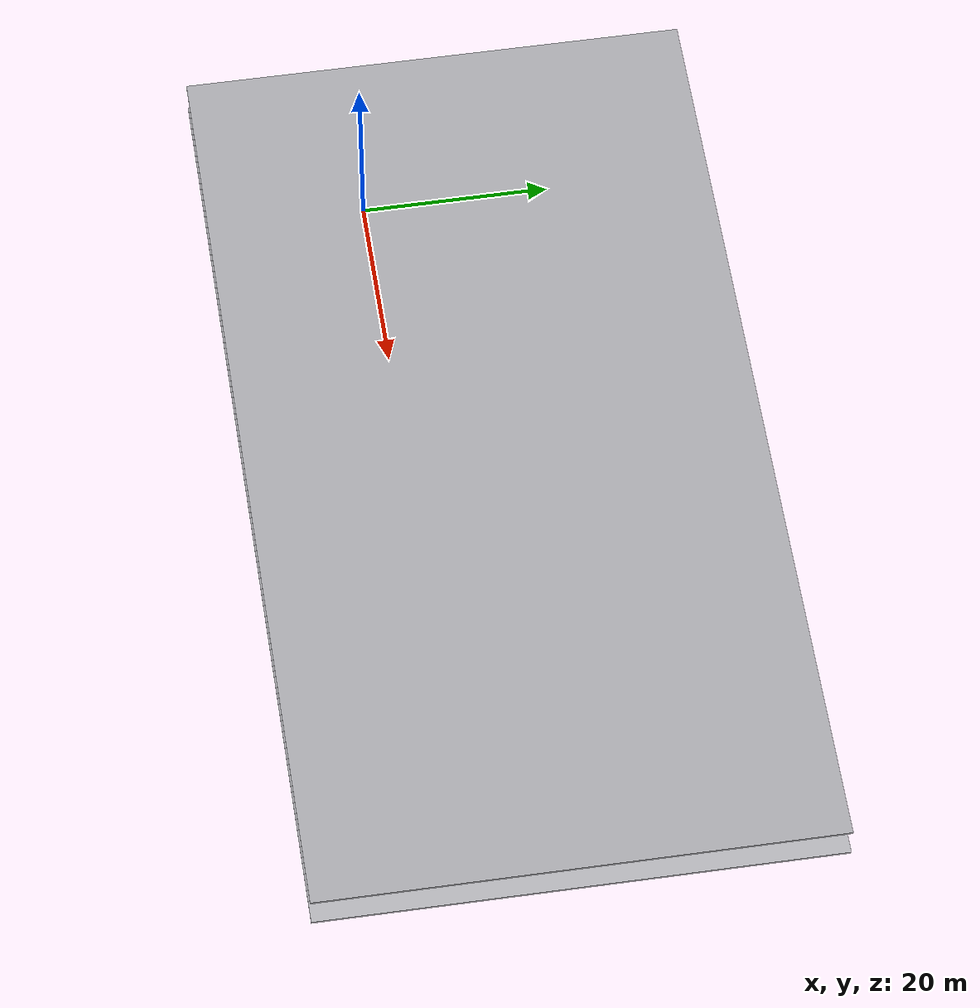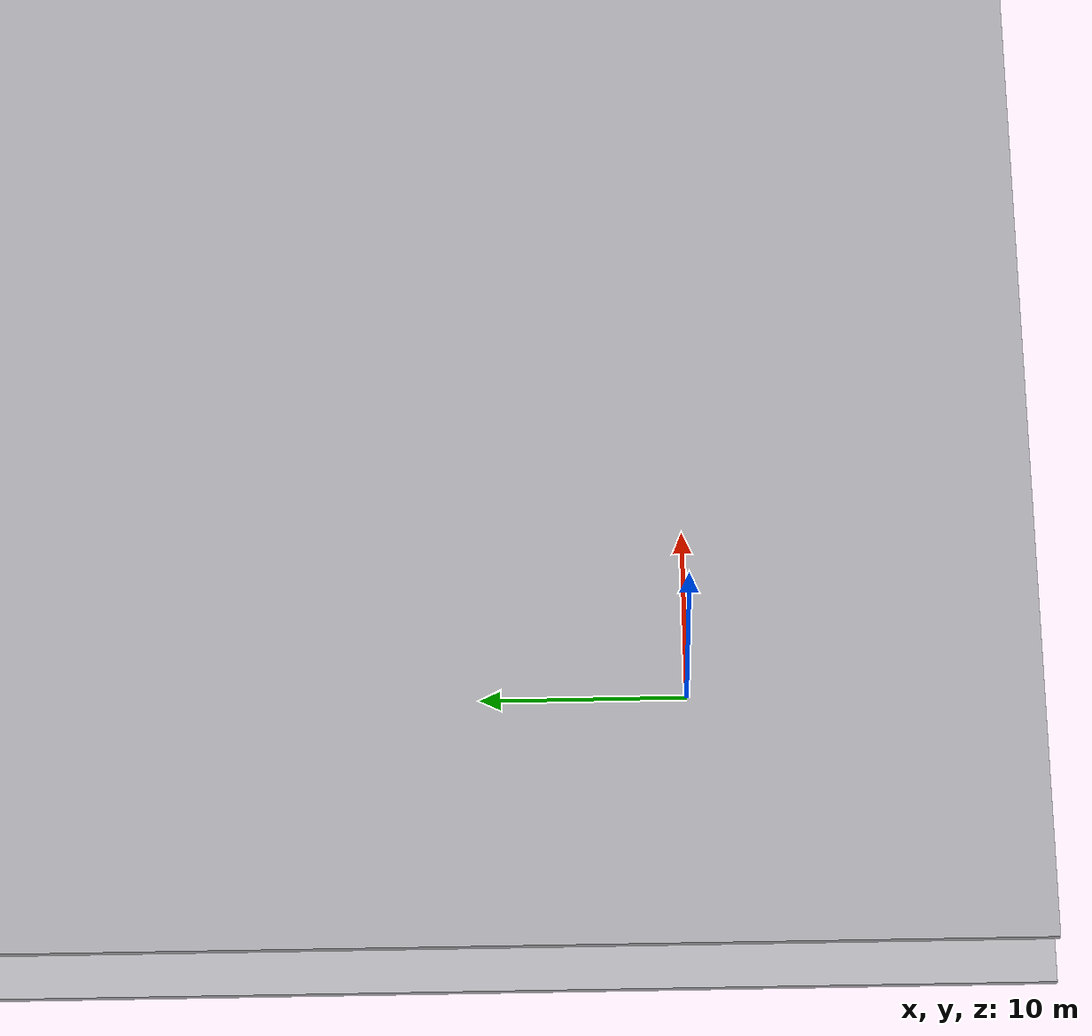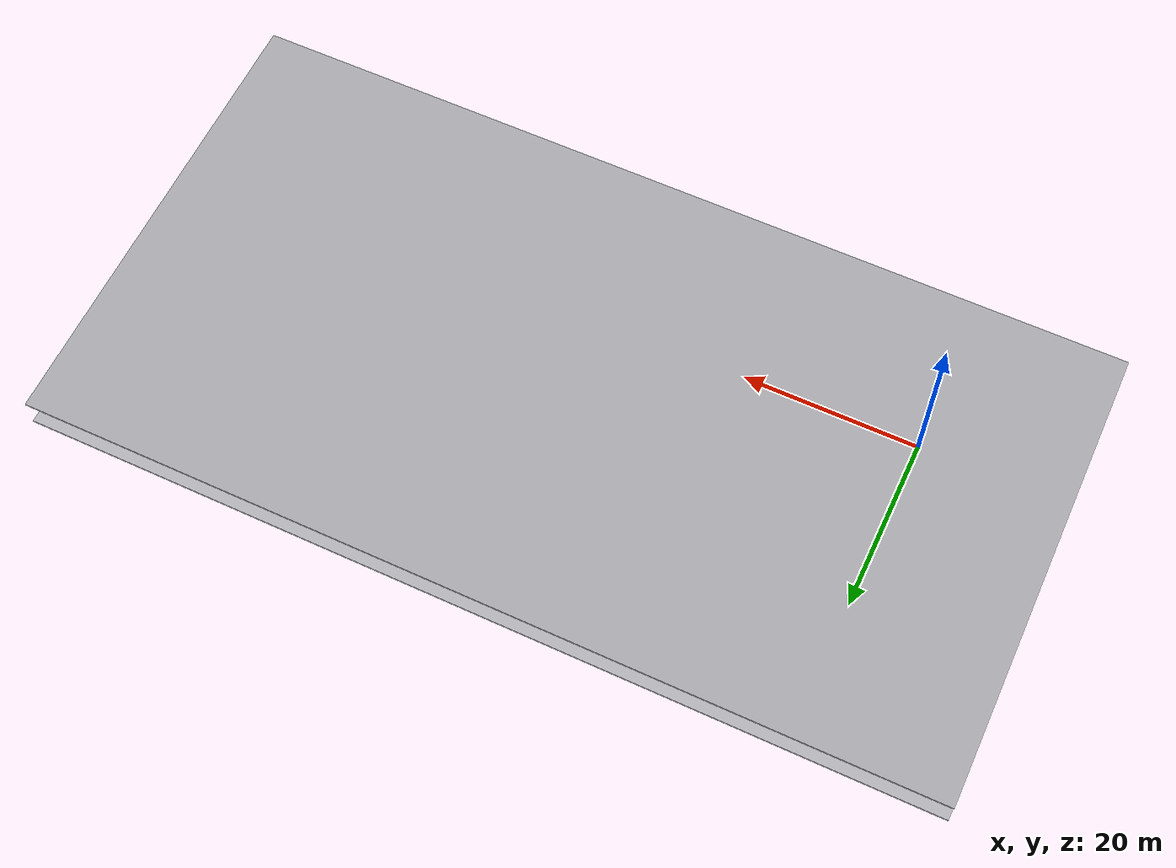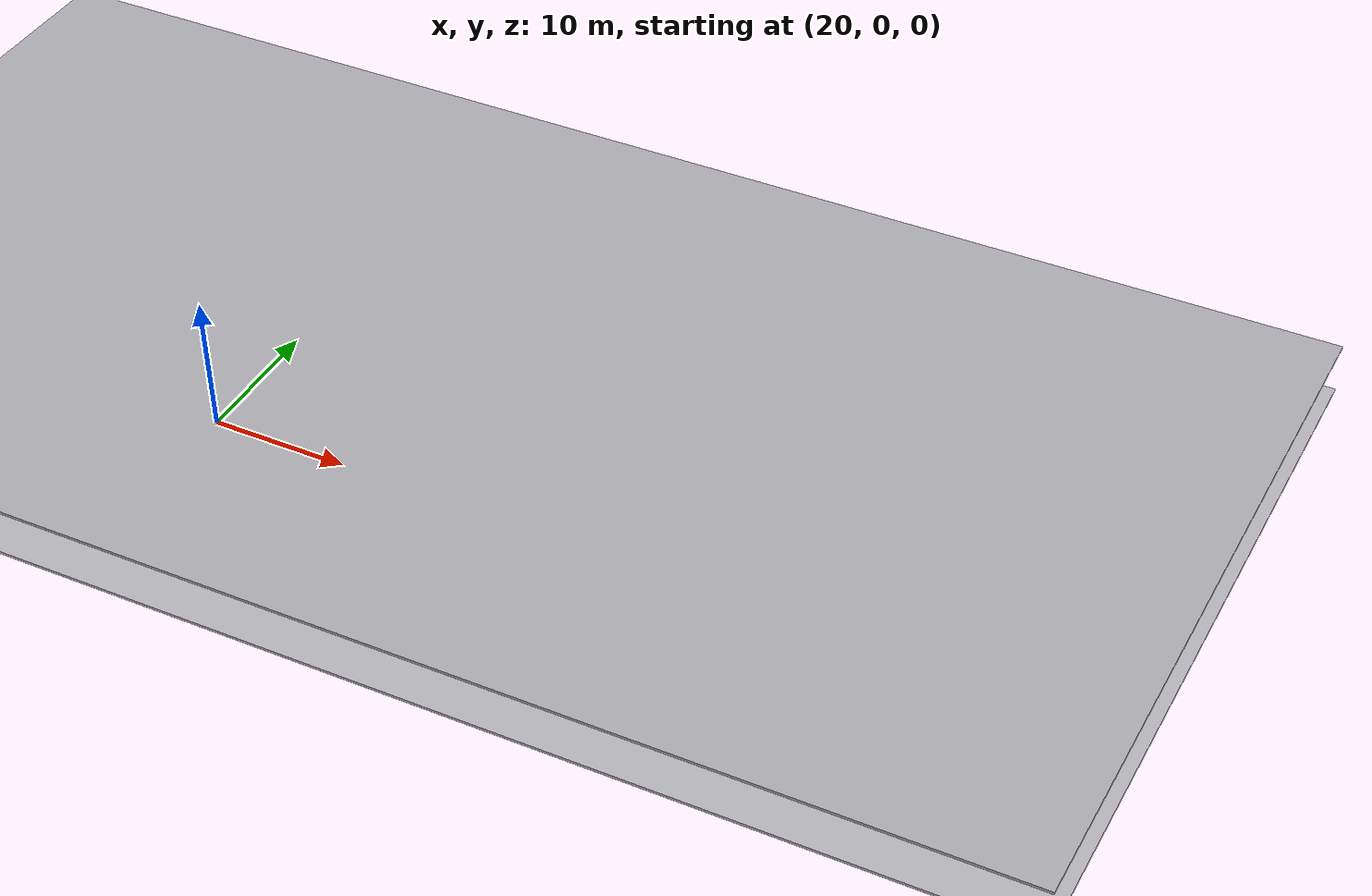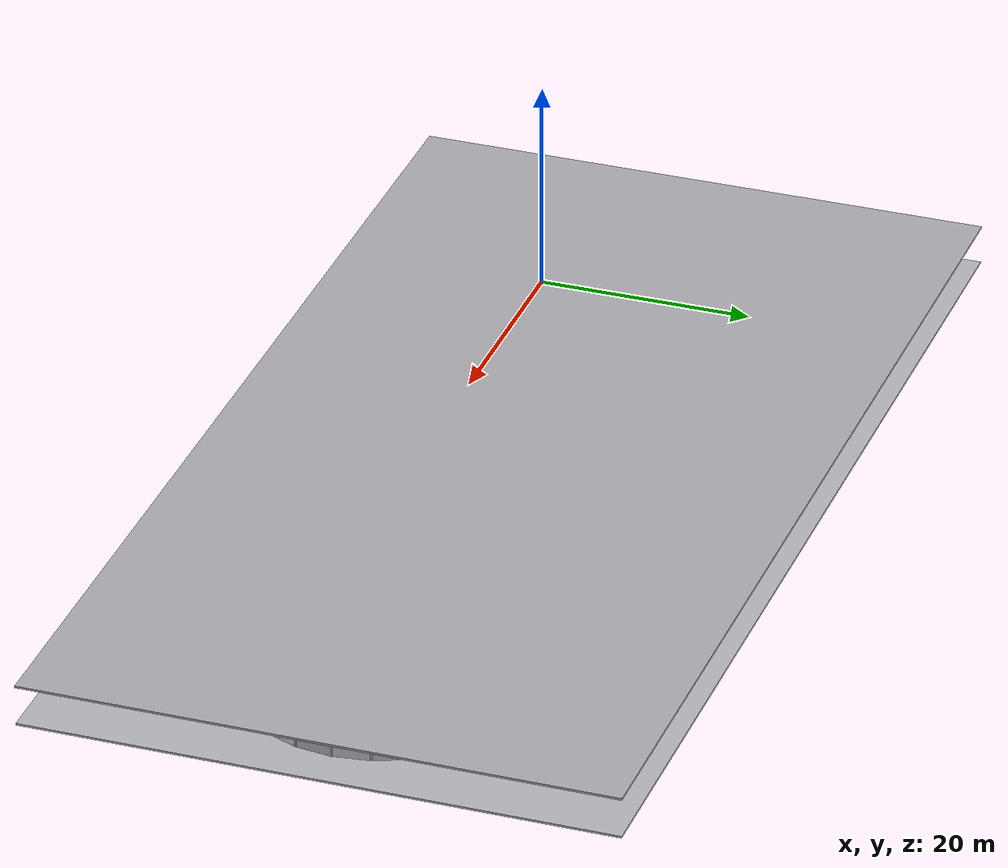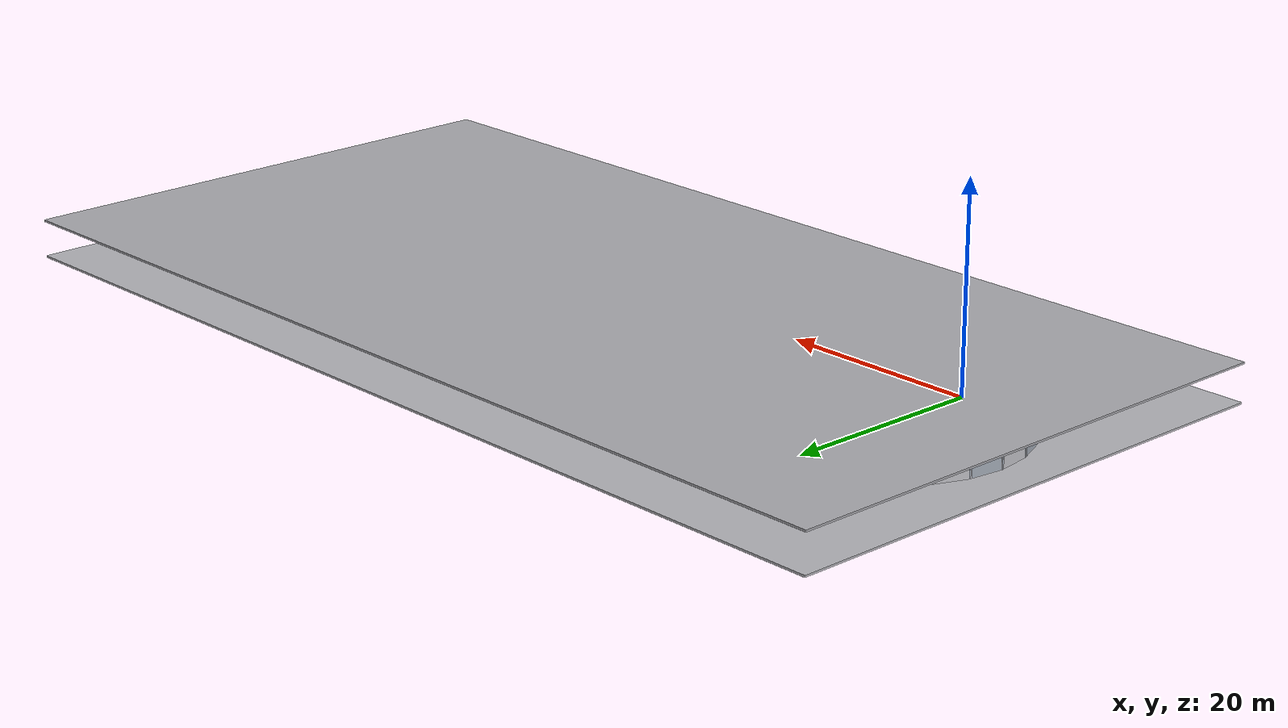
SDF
<?xml version="1.0" ?>
<sdf version="1.10">
  <world name="tunnel_circuit">

    <physics name="dartsim_250hz" type="dart">
      <max_step_size>0.004</max_step_size>
      <real_time_factor>0.5</real_time_factor>
      <real_time_update_rate>125</real_time_update_rate>
    </physics>

    <plugin filename="gz-sim-physics-system" name="gz::sim::systems::Physics"/>
    <plugin filename="gz-sim-user-commands-system" name="gz::sim::systems::UserCommands"/>
    <plugin filename="gz-sim-scene-broadcaster-system" name="gz::sim::systems::SceneBroadcaster"/>
    <plugin filename="gz-sim-contact-system" name="gz::sim::systems::Contact"/>
    <plugin filename="gz-sim-sensors-system" name="gz::sim::systems::Sensors">
      <render_engine>ogre2</render_engine>
    </plugin>
    <plugin filename="gz-sim-imu-system" name="gz::sim::systems::Imu"/>

    <scene>
      <ambient>0.32 0.32 0.35 1</ambient>
      <background>0.05 0.05 0.07 1</background>
      <grid>false</grid>
      <shadows>true</shadows>
    </scene>

    <light type="directional" name="fill">
      <pose>35.0 10.0 8 0 0 0</pose><direction>0.2 0.15 -1</direction>
      <diffuse>0.35 0.35 0.35 1</diffuse><specular>0.05 0.05 0.05 1</specular>
      <intensity>0.5</intensity><cast_shadows>false</cast_shadows>
    </light>
    <light type="point" name="light_t0">
      <pose>3.17 0.00 3.25 0 0 0</pose>
      <diffuse>0.95 0.93 0.85 1</diffuse><specular>0.2 0.2 0.2 1</specular><intensity>1.0</intensity>
      <attenuation><range>16</range><constant>0.3</constant><linear>0.07</linear><quadratic>0.01</quadratic></attenuation>
      <cast_shadows>true</cast_shadows>
    </light>
    <light type="point" name="light_t1">
      <pose>15.85 0.00 3.25 0 0 0</pose>
      <diffuse>0.95 0.93 0.85 1</diffuse><specular>0.2 0.2 0.2 1</specular><intensity>1.0</intensity>
      <attenuation><range>16</range><constant>0.3</constant><linear>0.07</linear><quadratic>0.01</quadratic></attenuation>
      <cast_shadows>false</cast_shadows>
    </light>
    <light type="point" name="light_t2">
      <pose>28.52 0.00 3.25 0 0 0</pose>
      <diffuse>0.95 0.93 0.85 1</diffuse><specular>0.2 0.2 0.2 1</specular><intensity>1.0</intensity>
      <attenuation><range>16</range><constant>0.3</constant><linear>0.07</linear><quadratic>0.01</quadratic></attenuation>
      <cast_shadows>false</cast_shadows>
    </light>
    <light type="point" name="light_t3">
      <pose>41.20 0.00 3.25 0 0 0</pose>
      <diffuse>0.95 0.93 0.85 1</diffuse><specular>0.2 0.2 0.2 1</specular><intensity>1.0</intensity>
      <attenuation><range>16</range><constant>0.3</constant><linear>0.07</linear><quadratic>0.01</quadratic></attenuation>
      <cast_shadows>false</cast_shadows>
    </light>
    <light type="point" name="light_t4">
      <pose>53.88 0.00 3.25 0 0 0</pose>
      <diffuse>0.95 0.93 0.85 1</diffuse><specular>0.2 0.2 0.2 1</specular><intensity>1.0</intensity>
      <attenuation><range>16</range><constant>0.3</constant><linear>0.07</linear><quadratic>0.01</quadratic></attenuation>
      <cast_shadows>true</cast_shadows>
    </light>
    <light type="point" name="light_t5">
      <pose>66.55 0.00 3.25 0 0 0</pose>
      <diffuse>0.95 0.93 0.85 1</diffuse><specular>0.2 0.2 0.2 1</specular><intensity>1.0</intensity>
      <attenuation><range>16</range><constant>0.3</constant><linear>0.07</linear><quadratic>0.01</quadratic></attenuation>
      <cast_shadows>false</cast_shadows>
    </light>
    <light type="point" name="light_t6">
      <pose>77.97 3.97 3.25 0 0 0</pose>
      <diffuse>0.95 0.93 0.85 1</diffuse><specular>0.2 0.2 0.2 1</specular><intensity>1.0</intensity>
      <attenuation><range>16</range><constant>0.3</constant><linear>0.07</linear><quadratic>0.01</quadratic></attenuation>
      <cast_shadows>false</cast_shadows>
    </light>
    <light type="point" name="light_t7">
      <pose>78.14 15.81 3.25 0 0 0</pose>
      <diffuse>0.95 0.93 0.85 1</diffuse><specular>0.2 0.2 0.2 1</specular><intensity>1.0</intensity>
      <attenuation><range>16</range><constant>0.3</constant><linear>0.07</linear><quadratic>0.01</quadratic></attenuation>
      <cast_shadows>false</cast_shadows>
    </light>
    <light type="point" name="light_t8">
      <pose>66.83 20.00 3.25 0 0 0</pose>
      <diffuse>0.95 0.93 0.85 1</diffuse><specular>0.2 0.2 0.2 1</specular><intensity>1.0</intensity>
      <attenuation><range>16</range><constant>0.3</constant><linear>0.07</linear><quadratic>0.01</quadratic></attenuation>
      <cast_shadows>true</cast_shadows>
    </light>
    <light type="point" name="light_t9">
      <pose>54.15 20.00 3.25 0 0 0</pose>
      <diffuse>0.95 0.93 0.85 1</diffuse><specular>0.2 0.2 0.2 1</specular><intensity>1.0</intensity>
      <attenuation><range>16</range><constant>0.3</constant><linear>0.07</linear><quadratic>0.01</quadratic></attenuation>
      <cast_shadows>false</cast_shadows>
    </light>
    <light type="point" name="light_t10">
      <pose>41.48 20.00 3.25 0 0 0</pose>
      <diffuse>0.95 0.93 0.85 1</diffuse><specular>0.2 0.2 0.2 1</specular><intensity>1.0</intensity>
      <attenuation><range>16</range><constant>0.3</constant><linear>0.07</linear><quadratic>0.01</quadratic></attenuation>
      <cast_shadows>false</cast_shadows>
    </light>
    <light type="point" name="light_t11">
      <pose>28.80 20.00 3.25 0 0 0</pose>
      <diffuse>0.95 0.93 0.85 1</diffuse><specular>0.2 0.2 0.2 1</specular><intensity>1.0</intensity>
      <attenuation><range>16</range><constant>0.3</constant><linear>0.07</linear><quadratic>0.01</quadratic></attenuation>
      <cast_shadows>false</cast_shadows>
    </light>
    <light type="point" name="light_t12">
      <pose>16.12 20.00 3.25 0 0 0</pose>
      <diffuse>0.95 0.93 0.85 1</diffuse><specular>0.2 0.2 0.2 1</specular><intensity>1.0</intensity>
      <attenuation><range>16</range><constant>0.3</constant><linear>0.07</linear><quadratic>0.01</quadratic></attenuation>
      <cast_shadows>true</cast_shadows>
    </light>
    <light type="point" name="light_t13">
      <pose>3.45 20.00 3.25 0 0 0</pose>
      <diffuse>0.95 0.93 0.85 1</diffuse><specular>0.2 0.2 0.2 1</specular><intensity>1.0</intensity>
      <attenuation><range>16</range><constant>0.3</constant><linear>0.07</linear><quadratic>0.01</quadratic></attenuation>
      <cast_shadows>false</cast_shadows>
    </light>
    <light type="point" name="light_t14">
      <pose>-7.97 16.03 3.25 0 0 0</pose>
      <diffuse>0.95 0.93 0.85 1</diffuse><specular>0.2 0.2 0.2 1</specular><intensity>1.0</intensity>
      <attenuation><range>16</range><constant>0.3</constant><linear>0.07</linear><quadratic>0.01</quadratic></attenuation>
      <cast_shadows>false</cast_shadows>
    </light>
    <light type="point" name="light_t15">
      <pose>-8.14 4.19 3.25 0 0 0</pose>
      <diffuse>0.95 0.93 0.85 1</diffuse><specular>0.2 0.2 0.2 1</specular><intensity>1.0</intensity>
      <attenuation><range>16</range><constant>0.3</constant><linear>0.07</linear><quadratic>0.01</quadratic></attenuation>
      <cast_shadows>false</cast_shadows>
    </light>

    <model name="floor">
      <static>true</static>
      <pose>35.000 10.000 -0.100 0 0 0.0000</pose>
      <link name="link">
        <collision name="col"><geometry><box><size>104.000 54.000 0.200</size></box></geometry></collision>
        <visual name="vis"><geometry><box><size>104.000 54.000 0.200</size></box></geometry>
          <material><ambient>0.40 0.40 0.42 1</ambient><diffuse>0.70 0.70 0.72 1</diffuse><specular>0.1 0.1 0.1 1</specular><pbr><metal><albedo_map>detail.png</albedo_map><roughness>0.95</roughness><metalness>0.0</metalness></metal></pbr></material></visual>
      </link>
    </model>

    <model name="ceiling">
      <static>true</static>
      <pose>35.000 10.000 3.600 0 0 0.0000</pose>
      <link name="link">
        <collision name="col"><geometry><box><size>104.000 54.000 0.200</size></box></geometry></collision>
        <visual name="vis"><geometry><box><size>104.000 54.000 0.200</size></box></geometry>
          <material><ambient>0.55 0.55 0.57 1</ambient><diffuse>0.66 0.66 0.68 1</diffuse><specular>0.1 0.1 0.1 1</specular></material></visual>
      </link>
    </model>

    <model name="tw_Ao_0">
      <static>true</static>
      <pose>2.500 -3.000 1.750 0 0 0.0000</pose>
      <link name="link">
        <collision name="col"><geometry><box><size>5.060 0.200 3.500</size></box></geometry></collision>
        <visual name="vis"><geometry><box><size>5.060 0.200 3.500</size></box></geometry>
          <material><ambient>0.50 0.50 0.52 1</ambient><diffuse>0.80 0.80 0.82 1</diffuse><specular>0.1 0.1 0.1 1</specular><pbr><metal><albedo_map>detail.png</albedo_map><roughness>0.92</roughness><metalness>0.0</metalness></metal></pbr></material></visual>
      </link>
    </model>
    <model name="tw_Ao_1">
      <static>true</static>
      <pose>7.500 -3.000 1.750 0 0 0.0000</pose>
      <link name="link">
        <collision name="col"><geometry><box><size>5.060 0.200 3.500</size></box></geometry></collision>
        <visual name="vis"><geometry><box><size>5.060 0.200 3.500</size></box></geometry>
          <material><ambient>0.42 0.44 0.48 1</ambient><diffuse>0.68 0.71 0.76 1</diffuse><specular>0.1 0.1 0.1 1</specular><pbr><metal><albedo_map>detail.png</albedo_map><roughness>0.9</roughness><metalness>0.0</metalness></metal></pbr></material></visual>
      </link>
    </model>
    <model name="tw_Ao_2">
      <static>true</static>
      <pose>12.500 -3.000 1.750 0 0 0.0000</pose>
      <link name="link">
        <collision name="col"><geometry><box><size>5.060 0.200 3.500</size></box></geometry></collision>
        <visual name="vis"><geometry><box><size>5.060 0.200 3.500</size></box></geometry>
          <material><ambient>0.50 0.50 0.52 1</ambient><diffuse>0.80 0.80 0.82 1</diffuse><specular>0.1 0.1 0.1 1</specular><pbr><metal><albedo_map>detail.png</albedo_map><roughness>0.92</roughness><metalness>0.0</metalness></metal></pbr></material></visual>
      </link>
    </model>
    <model name="tw_Ao_3">
      <static>true</static>
      <pose>17.500 -3.000 1.750 0 0 0.0000</pose>
      <link name="link">
        <collision name="col"><geometry><box><size>5.060 0.200 3.500</size></box></geometry></collision>
        <visual name="vis"><geometry><box><size>5.060 0.200 3.500</size></box></geometry>
          <material><ambient>0.42 0.44 0.48 1</ambient><diffuse>0.68 0.71 0.76 1</diffuse><specular>0.1 0.1 0.1 1</specular><pbr><metal><albedo_map>detail.png</albedo_map><roughness>0.9</roughness><metalness>0.0</metalness></metal></pbr></material></visual>
      </link>
    </model>
    <model name="tw_Ao_4">
      <static>true</static>
      <pose>22.500 -3.000 1.750 0 0 0.0000</pose>
      <link name="link">
        <collision name="col"><geometry><box><size>5.060 0.200 3.500</size></box></geometry></collision>
        <visual name="vis"><geometry><box><size>5.060 0.200 3.500</size></box></geometry>
          <material><ambient>0.50 0.50 0.52 1</ambient><diffuse>0.80 0.80 0.82 1</diffuse><specular>0.1 0.1 0.1 1</specular><pbr><metal><albedo_map>detail.png</albedo_map><roughness>0.92</roughness><metalness>0.0</metalness></metal></pbr></material></visual>
      </link>
    </model>
    <model name="tw_Ao_5">
      <static>true</static>
      <pose>27.500 -3.000 1.750 0 0 0.0000</pose>
      <link name="link">
        <collision name="col"><geometry><box><size>5.060 0.200 3.500</size></box></geometry></collision>
        <visual name="vis"><geometry><box><size>5.060 0.200 3.500</size></box></geometry>
          <material><ambient>0.42 0.44 0.48 1</ambient><diffuse>0.68 0.71 0.76 1</diffuse><specular>0.1 0.1 0.1 1</specular><pbr><metal><albedo_map>detail.png</albedo_map><roughness>0.9</roughness><metalness>0.0</metalness></metal></pbr></material></visual>
      </link>
    </model>
    <model name="tw_Ao_6">
      <static>true</static>
      <pose>32.500 -3.000 1.750 0 0 0.0000</pose>
      <link name="link">
        <collision name="col"><geometry><box><size>5.060 0.200 3.500</size></box></geometry></collision>
        <visual name="vis"><geometry><box><size>5.060 0.200 3.500</size></box></geometry>
          <material><ambient>0.50 0.50 0.52 1</ambient><diffuse>0.80 0.80 0.82 1</diffuse><specular>0.1 0.1 0.1 1</specular><pbr><metal><albedo_map>detail.png</albedo_map><roughness>0.92</roughness><metalness>0.0</metalness></metal></pbr></material></visual>
      </link>
    </model>
    <model name="tw_Ao_7">
      <static>true</static>
      <pose>37.500 -3.000 1.750 0 0 0.0000</pose>
      <link name="link">
        <collision name="col"><geometry><box><size>5.060 0.200 3.500</size></box></geometry></collision>
        <visual name="vis"><geometry><box><size>5.060 0.200 3.500</size></box></geometry>
          <material><ambient>0.42 0.44 0.48 1</ambient><diffuse>0.68 0.71 0.76 1</diffuse><specular>0.1 0.1 0.1 1</specular><pbr><metal><albedo_map>detail.png</albedo_map><roughness>0.9</roughness><metalness>0.0</metalness></metal></pbr></material></visual>
      </link>
    </model>
    <model name="tw_Ao_8">
      <static>true</static>
      <pose>42.500 -3.000 1.750 0 0 0.0000</pose>
      <link name="link">
        <collision name="col"><geometry><box><size>5.060 0.200 3.500</size></box></geometry></collision>
        <visual name="vis"><geometry><box><size>5.060 0.200 3.500</size></box></geometry>
          <material><ambient>0.50 0.50 0.52 1</ambient><diffuse>0.80 0.80 0.82 1</diffuse><specular>0.1 0.1 0.1 1</specular><pbr><metal><albedo_map>detail.png</albedo_map><roughness>0.92</roughness><metalness>0.0</metalness></metal></pbr></material></visual>
      </link>
    </model>
    <model name="tw_Ao_9">
      <static>true</static>
      <pose>47.500 -3.000 1.750 0 0 0.0000</pose>
      <link name="link">
        <collision name="col"><geometry><box><size>5.060 0.200 3.500</size></box></geometry></collision>
        <visual name="vis"><geometry><box><size>5.060 0.200 3.500</size></box></geometry>
          <material><ambient>0.42 0.44 0.48 1</ambient><diffuse>0.68 0.71 0.76 1</diffuse><specular>0.1 0.1 0.1 1</specular><pbr><metal><albedo_map>detail.png</albedo_map><roughness>0.9</roughness><metalness>0.0</metalness></metal></pbr></material></visual>
      </link>
    </model>
    <model name="tw_Ao_10">
      <static>true</static>
      <pose>52.500 -3.000 1.750 0 0 0.0000</pose>
      <link name="link">
        <collision name="col"><geometry><box><size>5.060 0.200 3.500</size></box></geometry></collision>
        <visual name="vis"><geometry><box><size>5.060 0.200 3.500</size></box></geometry>
          <material><ambient>0.50 0.50 0.52 1</ambient><diffuse>0.80 0.80 0.82 1</diffuse><specular>0.1 0.1 0.1 1</specular><pbr><metal><albedo_map>detail.png</albedo_map><roughness>0.92</roughness><metalness>0.0</metalness></metal></pbr></material></visual>
      </link>
    </model>
    <model name="tw_Ao_11">
      <static>true</static>
      <pose>57.500 -3.000 1.750 0 0 0.0000</pose>
      <link name="link">
        <collision name="col"><geometry><box><size>5.060 0.200 3.500</size></box></geometry></collision>
        <visual name="vis"><geometry><box><size>5.060 0.200 3.500</size></box></geometry>
          <material><ambient>0.42 0.44 0.48 1</ambient><diffuse>0.68 0.71 0.76 1</diffuse><specular>0.1 0.1 0.1 1</specular><pbr><metal><albedo_map>detail.png</albedo_map><roughness>0.9</roughness><metalness>0.0</metalness></metal></pbr></material></visual>
      </link>
    </model>
    <model name="tw_Ao_12">
      <static>true</static>
      <pose>62.500 -3.000 1.750 0 0 0.0000</pose>
      <link name="link">
        <collision name="col"><geometry><box><size>5.060 0.200 3.500</size></box></geometry></collision>
        <visual name="vis"><geometry><box><size>5.060 0.200 3.500</size></box></geometry>
          <material><ambient>0.50 0.50 0.52 1</ambient><diffuse>0.80 0.80 0.82 1</diffuse><specular>0.1 0.1 0.1 1</specular><pbr><metal><albedo_map>detail.png</albedo_map><roughness>0.92</roughness><metalness>0.0</metalness></metal></pbr></material></visual>
      </link>
    </model>
    <model name="tw_Ao_13">
      <static>true</static>
      <pose>67.500 -3.000 1.750 0 0 0.0000</pose>
      <link name="link">
        <collision name="col"><geometry><box><size>5.060 0.200 3.500</size></box></geometry></collision>
        <visual name="vis"><geometry><box><size>5.060 0.200 3.500</size></box></geometry>
          <material><ambient>0.42 0.44 0.48 1</ambient><diffuse>0.68 0.71 0.76 1</diffuse><specular>0.1 0.1 0.1 1</specular><pbr><metal><albedo_map>detail.png</albedo_map><roughness>0.9</roughness><metalness>0.0</metalness></metal></pbr></material></visual>
      </link>
    </model>

    <model name="tw_Ai_0">
      <static>true</static>
      <pose>2.500 3.000 1.750 0 0 0.0000</pose>
      <link name="link">
        <collision name="col"><geometry><box><size>5.060 0.200 3.500</size></box></geometry></collision>
        <visual name="vis"><geometry><box><size>5.060 0.200 3.500</size></box></geometry>
          <material><ambient>0.50 0.50 0.52 1</ambient><diffuse>0.80 0.80 0.82 1</diffuse><specular>0.1 0.1 0.1 1</specular><pbr><metal><albedo_map>detail.png</albedo_map><roughness>0.92</roughness><metalness>0.0</metalness></metal></pbr></material></visual>
      </link>
    </model>
    <model name="tw_Ai_1">
      <static>true</static>
      <pose>7.500 3.000 1.750 0 0 0.0000</pose>
      <link name="link">
        <collision name="col"><geometry><box><size>5.060 0.200 3.500</size></box></geometry></collision>
        <visual name="vis"><geometry><box><size>5.060 0.200 3.500</size></box></geometry>
          <material><ambient>0.42 0.44 0.48 1</ambient><diffuse>0.68 0.71 0.76 1</diffuse><specular>0.1 0.1 0.1 1</specular><pbr><metal><albedo_map>detail.png</albedo_map><roughness>0.9</roughness><metalness>0.0</metalness></metal></pbr></material></visual>
      </link>
    </model>
    <model name="tw_Ai_2">
      <static>true</static>
      <pose>12.500 3.000 1.750 0 0 0.0000</pose>
      <link name="link">
        <collision name="col"><geometry><box><size>5.060 0.200 3.500</size></box></geometry></collision>
        <visual name="vis"><geometry><box><size>5.060 0.200 3.500</size></box></geometry>
          <material><ambient>0.50 0.50 0.52 1</ambient><diffuse>0.80 0.80 0.82 1</diffuse><specular>0.1 0.1 0.1 1</specular><pbr><metal><albedo_map>detail.png</albedo_map><roughness>0.92</roughness><metalness>0.0</metalness></metal></pbr></material></visual>
      </link>
    </model>
    <model name="tw_Ai_3">
      <static>true</static>
      <pose>17.500 3.000 1.750 0 0 0.0000</pose>
      <link name="link">
        <collision name="col"><geometry><box><size>5.060 0.200 3.500</size></box></geometry></collision>
        <visual name="vis"><geometry><box><size>5.060 0.200 3.500</size></box></geometry>
          <material><ambient>0.42 0.44 0.48 1</ambient><diffuse>0.68 0.71 0.76 1</diffuse><specular>0.1 0.1 0.1 1</specular><pbr><metal><albedo_map>detail.png</albedo_map><roughness>0.9</roughness><metalness>0.0</metalness></metal></pbr></material></visual>
      </link>
    </model>
    <model name="tw_Ai_4">
      <static>true</static>
      <pose>22.500 3.000 1.750 0 0 0.0000</pose>
      <link name="link">
        <collision name="col"><geometry><box><size>5.060 0.200 3.500</size></box></geometry></collision>
        <visual name="vis"><geometry><box><size>5.060 0.200 3.500</size></box></geometry>
          <material><ambient>0.50 0.50 0.52 1</ambient><diffuse>0.80 0.80 0.82 1</diffuse><specular>0.1 0.1 0.1 1</specular><pbr><metal><albedo_map>detail.png</albedo_map><roughness>0.92</roughness><metalness>0.0</metalness></metal></pbr></material></visual>
      </link>
    </model>
    <model name="tw_Ai_5">
      <static>true</static>
      <pose>27.500 3.000 1.750 0 0 0.0000</pose>
      <link name="link">
        <collision name="col"><geometry><box><size>5.060 0.200 3.500</size></box></geometry></collision>
        <visual name="vis"><geometry><box><size>5.060 0.200 3.500</size></box></geometry>
          <material><ambient>0.42 0.44 0.48 1</ambient><diffuse>0.68 0.71 0.76 1</diffuse><specular>0.1 0.1 0.1 1</specular><pbr><metal><albedo_map>detail.png</albedo_map><roughness>0.9</roughness><metalness>0.0</metalness></metal></pbr></material></visual>
      </link>
    </model>
    <model name="tw_Ai_6">
      <static>true</static>
      <pose>32.500 3.000 1.750 0 0 0.0000</pose>
      <link name="link">
        <collision name="col"><geometry><box><size>5.060 0.200 3.500</size></box></geometry></collision>
        <visual name="vis"><geometry><box><size>5.060 0.200 3.500</size></box></geometry>
          <material><ambient>0.50 0.50 0.52 1</ambient><diffuse>0.80 0.80 0.82 1</diffuse><specular>0.1 0.1 0.1 1</specular><pbr><metal><albedo_map>detail.png</albedo_map><roughness>0.92</roughness><metalness>0.0</metalness></metal></pbr></material></visual>
      </link>
    </model>
    <model name="tw_Ai_7">
      <static>true</static>
      <pose>37.500 3.000 1.750 0 0 0.0000</pose>
      <link name="link">
        <collision name="col"><geometry><box><size>5.060 0.200 3.500</size></box></geometry></collision>
        <visual name="vis"><geometry><box><size>5.060 0.200 3.500</size></box></geometry>
          <material><ambient>0.42 0.44 0.48 1</ambient><diffuse>0.68 0.71 0.76 1</diffuse><specular>0.1 0.1 0.1 1</specular><pbr><metal><albedo_map>detail.png</albedo_map><roughness>0.9</roughness><metalness>0.0</metalness></metal></pbr></material></visual>
      </link>
    </model>
    <model name="tw_Ai_8">
      <static>true</static>
      <pose>42.500 3.000 1.750 0 0 0.0000</pose>
      <link name="link">
        <collision name="col"><geometry><box><size>5.060 0.200 3.500</size></box></geometry></collision>
        <visual name="vis"><geometry><box><size>5.060 0.200 3.500</size></box></geometry>
          <material><ambient>0.50 0.50 0.52 1</ambient><diffuse>0.80 0.80 0.82 1</diffuse><specular>0.1 0.1 0.1 1</specular><pbr><metal><albedo_map>detail.png</albedo_map><roughness>0.92</roughness><metalness>0.0</metalness></metal></pbr></material></visual>
      </link>
    </model>
    <model name="tw_Ai_9">
      <static>true</static>
      <pose>47.500 3.000 1.750 0 0 0.0000</pose>
      <link name="link">
        <collision name="col"><geometry><box><size>5.060 0.200 3.500</size></box></geometry></collision>
        <visual name="vis"><geometry><box><size>5.060 0.200 3.500</size></box></geometry>
          <material><ambient>0.42 0.44 0.48 1</ambient><diffuse>0.68 0.71 0.76 1</diffuse><specular>0.1 0.1 0.1 1</specular><pbr><metal><albedo_map>detail.png</albedo_map><roughness>0.9</roughness><metalness>0.0</metalness></metal></pbr></material></visual>
      </link>
    </model>
    <model name="tw_Ai_10">
      <static>true</static>
      <pose>52.500 3.000 1.750 0 0 0.0000</pose>
      <link name="link">
        <collision name="col"><geometry><box><size>5.060 0.200 3.500</size></box></geometry></collision>
        <visual name="vis"><geometry><box><size>5.060 0.200 3.500</size></box></geometry>
          <material><ambient>0.50 0.50 0.52 1</ambient><diffuse>0.80 0.80 0.82 1</diffuse><specular>0.1 0.1 0.1 1</specular><pbr><metal><albedo_map>detail.png</albedo_map><roughness>0.92</roughness><metalness>0.0</metalness></metal></pbr></material></visual>
      </link>
    </model>
    <model name="tw_Ai_11">
      <static>true</static>
      <pose>57.500 3.000 1.750 0 0 0.0000</pose>
      <link name="link">
        <collision name="col"><geometry><box><size>5.060 0.200 3.500</size></box></geometry></collision>
        <visual name="vis"><geometry><box><size>5.060 0.200 3.500</size></box></geometry>
          <material><ambient>0.42 0.44 0.48 1</ambient><diffuse>0.68 0.71 0.76 1</diffuse><specular>0.1 0.1 0.1 1</specular><pbr><metal><albedo_map>detail.png</albedo_map><roughness>0.9</roughness><metalness>0.0</metalness></metal></pbr></material></visual>
      </link>
    </model>
    <model name="tw_Ai_12">
      <static>true</static>
      <pose>62.500 3.000 1.750 0 0 0.0000</pose>
      <link name="link">
        <collision name="col"><geometry><box><size>5.060 0.200 3.500</size></box></geometry></collision>
        <visual name="vis"><geometry><box><size>5.060 0.200 3.500</size></box></geometry>
          <material><ambient>0.50 0.50 0.52 1</ambient><diffuse>0.80 0.80 0.82 1</diffuse><specular>0.1 0.1 0.1 1</specular><pbr><metal><albedo_map>detail.png</albedo_map><roughness>0.92</roughness><metalness>0.0</metalness></metal></pbr></material></visual>
      </link>
    </model>
    <model name="tw_Ai_13">
      <static>true</static>
      <pose>67.500 3.000 1.750 0 0 0.0000</pose>
      <link name="link">
        <collision name="col"><geometry><box><size>5.060 0.200 3.500</size></box></geometry></collision>
        <visual name="vis"><geometry><box><size>5.060 0.200 3.500</size></box></geometry>
          <material><ambient>0.42 0.44 0.48 1</ambient><diffuse>0.68 0.71 0.76 1</diffuse><specular>0.1 0.1 0.1 1</specular><pbr><metal><albedo_map>detail.png</albedo_map><roughness>0.9</roughness><metalness>0.0</metalness></metal></pbr></material></visual>
      </link>
    </model>

    <model name="tw_Bo_0">
      <static>true</static>
      <pose>2.500 23.000 1.750 0 0 0.0000</pose>
      <link name="link">
        <collision name="col"><geometry><box><size>5.060 0.200 3.500</size></box></geometry></collision>
        <visual name="vis"><geometry><box><size>5.060 0.200 3.500</size></box></geometry>
          <material><ambient>0.50 0.50 0.52 1</ambient><diffuse>0.80 0.80 0.82 1</diffuse><specular>0.1 0.1 0.1 1</specular><pbr><metal><albedo_map>detail.png</albedo_map><roughness>0.92</roughness><metalness>0.0</metalness></metal></pbr></material></visual>
      </link>
    </model>
    <model name="tw_Bo_1">
      <static>true</static>
      <pose>7.500 23.000 1.750 0 0 0.0000</pose>
      <link name="link">
        <collision name="col"><geometry><box><size>5.060 0.200 3.500</size></box></geometry></collision>
        <visual name="vis"><geometry><box><size>5.060 0.200 3.500</size></box></geometry>
          <material><ambient>0.42 0.44 0.48 1</ambient><diffuse>0.68 0.71 0.76 1</diffuse><specular>0.1 0.1 0.1 1</specular><pbr><metal><albedo_map>detail.png</albedo_map><roughness>0.9</roughness><metalness>0.0</metalness></metal></pbr></material></visual>
      </link>
    </model>
    <model name="tw_Bo_2">
      <static>true</static>
      <pose>12.500 23.000 1.750 0 0 0.0000</pose>
      <link name="link">
        <collision name="col"><geometry><box><size>5.060 0.200 3.500</size></box></geometry></collision>
        <visual name="vis"><geometry><box><size>5.060 0.200 3.500</size></box></geometry>
          <material><ambient>0.50 0.50 0.52 1</ambient><diffuse>0.80 0.80 0.82 1</diffuse><specular>0.1 0.1 0.1 1</specular><pbr><metal><albedo_map>detail.png</albedo_map><roughness>0.92</roughness><metalness>0.0</metalness></metal></pbr></material></visual>
      </link>
    </model>
    <model name="tw_Bo_3">
      <static>true</static>
      <pose>17.500 23.000 1.750 0 0 0.0000</pose>
      <link name="link">
        <collision name="col"><geometry><box><size>5.060 0.200 3.500</size></box></geometry></collision>
        <visual name="vis"><geometry><box><size>5.060 0.200 3.500</size></box></geometry>
          <material><ambient>0.42 0.44 0.48 1</ambient><diffuse>0.68 0.71 0.76 1</diffuse><specular>0.1 0.1 0.1 1</specular><pbr><metal><albedo_map>detail.png</albedo_map><roughness>0.9</roughness><metalness>0.0</metalness></metal></pbr></material></visual>
      </link>
    </model>
    <model name="tw_Bo_4">
      <static>true</static>
      <pose>22.500 23.000 1.750 0 0 0.0000</pose>
      <link name="link">
        <collision name="col"><geometry><box><size>5.060 0.200 3.500</size></box></geometry></collision>
        <visual name="vis"><geometry><box><size>5.060 0.200 3.500</size></box></geometry>
          <material><ambient>0.50 0.50 0.52 1</ambient><diffuse>0.80 0.80 0.82 1</diffuse><specular>0.1 0.1 0.1 1</specular><pbr><metal><albedo_map>detail.png</albedo_map><roughness>0.92</roughness><metalness>0.0</metalness></metal></pbr></material></visual>
      </link>
    </model>
    <model name="tw_Bo_5">
      <static>true</static>
      <pose>27.500 23.000 1.750 0 0 0.0000</pose>
      <link name="link">
        <collision name="col"><geometry><box><size>5.060 0.200 3.500</size></box></geometry></collision>
        <visual name="vis"><geometry><box><size>5.060 0.200 3.500</size></box></geometry>
          <material><ambient>0.42 0.44 0.48 1</ambient><diffuse>0.68 0.71 0.76 1</diffuse><specular>0.1 0.1 0.1 1</specular><pbr><metal><albedo_map>detail.png</albedo_map><roughness>0.9</roughness><metalness>0.0</metalness></metal></pbr></material></visual>
      </link>
    </model>
    <model name="tw_Bo_6">
      <static>true</static>
      <pose>32.500 23.000 1.750 0 0 0.0000</pose>
      <link name="link">
        <collision name="col"><geometry><box><size>5.060 0.200 3.500</size></box></geometry></collision>
        <visual name="vis"><geometry><box><size>5.060 0.200 3.500</size></box></geometry>
          <material><ambient>0.50 0.50 0.52 1</ambient><diffuse>0.80 0.80 0.82 1</diffuse><specular>0.1 0.1 0.1 1</specular><pbr><metal><albedo_map>detail.png</albedo_map><roughness>0.92</roughness><metalness>0.0</metalness></metal></pbr></material></visual>
      </link>
    </model>
    <model name="tw_Bo_7">
      <static>true</static>
      <pose>37.500 23.000 1.750 0 0 0.0000</pose>
      <link name="link">
        <collision name="col"><geometry><box><size>5.060 0.200 3.500</size></box></geometry></collision>
        <visual name="vis"><geometry><box><size>5.060 0.200 3.500</size></box></geometry>
          <material><ambient>0.42 0.44 0.48 1</ambient><diffuse>0.68 0.71 0.76 1</diffuse><specular>0.1 0.1 0.1 1</specular><pbr><metal><albedo_map>detail.png</albedo_map><roughness>0.9</roughness><metalness>0.0</metalness></metal></pbr></material></visual>
      </link>
    </model>
    <model name="tw_Bo_8">
      <static>true</static>
      <pose>42.500 23.000 1.750 0 0 0.0000</pose>
      <link name="link">
        <collision name="col"><geometry><box><size>5.060 0.200 3.500</size></box></geometry></collision>
        <visual name="vis"><geometry><box><size>5.060 0.200 3.500</size></box></geometry>
          <material><ambient>0.50 0.50 0.52 1</ambient><diffuse>0.80 0.80 0.82 1</diffuse><specular>0.1 0.1 0.1 1</specular><pbr><metal><albedo_map>detail.png</albedo_map><roughness>0.92</roughness><metalness>0.0</metalness></metal></pbr></material></visual>
      </link>
    </model>
    <model name="tw_Bo_9">
      <static>true</static>
      <pose>47.500 23.000 1.750 0 0 0.0000</pose>
      <link name="link">
        <collision name="col"><geometry><box><size>5.060 0.200 3.500</size></box></geometry></collision>
        <visual name="vis"><geometry><box><size>5.060 0.200 3.500</size></box></geometry>
          <material><ambient>0.42 0.44 0.48 1</ambient><diffuse>0.68 0.71 0.76 1</diffuse><specular>0.1 0.1 0.1 1</specular><pbr><metal><albedo_map>detail.png</albedo_map><roughness>0.9</roughness><metalness>0.0</metalness></metal></pbr></material></visual>
      </link>
    </model>
    <model name="tw_Bo_10">
      <static>true</static>
      <pose>52.500 23.000 1.750 0 0 0.0000</pose>
      <link name="link">
        <collision name="col"><geometry><box><size>5.060 0.200 3.500</size></box></geometry></collision>
        <visual name="vis"><geometry><box><size>5.060 0.200 3.500</size></box></geometry>
          <material><ambient>0.50 0.50 0.52 1</ambient><diffuse>0.80 0.80 0.82 1</diffuse><specular>0.1 0.1 0.1 1</specular><pbr><metal><albedo_map>detail.png</albedo_map><roughness>0.92</roughness><metalness>0.0</metalness></metal></pbr></material></visual>
      </link>
    </model>
    <model name="tw_Bo_11">
      <static>true</static>
      <pose>57.500 23.000 1.750 0 0 0.0000</pose>
      <link name="link">
        <collision name="col"><geometry><box><size>5.060 0.200 3.500</size></box></geometry></collision>
        <visual name="vis"><geometry><box><size>5.060 0.200 3.500</size></box></geometry>
          <material><ambient>0.42 0.44 0.48 1</ambient><diffuse>0.68 0.71 0.76 1</diffuse><specular>0.1 0.1 0.1 1</specular><pbr><metal><albedo_map>detail.png</albedo_map><roughness>0.9</roughness><metalness>0.0</metalness></metal></pbr></material></visual>
      </link>
    </model>
    <model name="tw_Bo_12">
      <static>true</static>
      <pose>62.500 23.000 1.750 0 0 0.0000</pose>
      <link name="link">
        <collision name="col"><geometry><box><size>5.060 0.200 3.500</size></box></geometry></collision>
        <visual name="vis"><geometry><box><size>5.060 0.200 3.500</size></box></geometry>
          <material><ambient>0.50 0.50 0.52 1</ambient><diffuse>0.80 0.80 0.82 1</diffuse><specular>0.1 0.1 0.1 1</specular><pbr><metal><albedo_map>detail.png</albedo_map><roughness>0.92</roughness><metalness>0.0</metalness></metal></pbr></material></visual>
      </link>
    </model>
    <model name="tw_Bo_13">
      <static>true</static>
      <pose>67.500 23.000 1.750 0 0 0.0000</pose>
      <link name="link">
        <collision name="col"><geometry><box><size>5.060 0.200 3.500</size></box></geometry></collision>
        <visual name="vis"><geometry><box><size>5.060 0.200 3.500</size></box></geometry>
          <material><ambient>0.42 0.44 0.48 1</ambient><diffuse>0.68 0.71 0.76 1</diffuse><specular>0.1 0.1 0.1 1</specular><pbr><metal><albedo_map>detail.png</albedo_map><roughness>0.9</roughness><metalness>0.0</metalness></metal></pbr></material></visual>
      </link>
    </model>

    <model name="tw_Bi_0">
      <static>true</static>
      <pose>2.500 17.000 1.750 0 0 0.0000</pose>
      <link name="link">
        <collision name="col"><geometry><box><size>5.060 0.200 3.500</size></box></geometry></collision>
        <visual name="vis"><geometry><box><size>5.060 0.200 3.500</size></box></geometry>
          <material><ambient>0.50 0.50 0.52 1</ambient><diffuse>0.80 0.80 0.82 1</diffuse><specular>0.1 0.1 0.1 1</specular><pbr><metal><albedo_map>detail.png</albedo_map><roughness>0.92</roughness><metalness>0.0</metalness></metal></pbr></material></visual>
      </link>
    </model>
    <model name="tw_Bi_1">
      <static>true</static>
      <pose>7.500 17.000 1.750 0 0 0.0000</pose>
      <link name="link">
        <collision name="col"><geometry><box><size>5.060 0.200 3.500</size></box></geometry></collision>
        <visual name="vis"><geometry><box><size>5.060 0.200 3.500</size></box></geometry>
          <material><ambient>0.42 0.44 0.48 1</ambient><diffuse>0.68 0.71 0.76 1</diffuse><specular>0.1 0.1 0.1 1</specular><pbr><metal><albedo_map>detail.png</albedo_map><roughness>0.9</roughness><metalness>0.0</metalness></metal></pbr></material></visual>
      </link>
    </model>
    <model name="tw_Bi_2">
      <static>true</static>
      <pose>12.500 17.000 1.750 0 0 0.0000</pose>
      <link name="link">
        <collision name="col"><geometry><box><size>5.060 0.200 3.500</size></box></geometry></collision>
        <visual name="vis"><geometry><box><size>5.060 0.200 3.500</size></box></geometry>
          <material><ambient>0.50 0.50 0.52 1</ambient><diffuse>0.80 0.80 0.82 1</diffuse><specular>0.1 0.1 0.1 1</specular><pbr><metal><albedo_map>detail.png</albedo_map><roughness>0.92</roughness><metalness>0.0</metalness></metal></pbr></material></visual>
      </link>
    </model>
    <model name="tw_Bi_3">
      <static>true</static>
      <pose>17.500 17.000 1.750 0 0 0.0000</pose>
      <link name="link">
        <collision name="col"><geometry><box><size>5.060 0.200 3.500</size></box></geometry></collision>
        <visual name="vis"><geometry><box><size>5.060 0.200 3.500</size></box></geometry>
          <material><ambient>0.42 0.44 0.48 1</ambient><diffuse>0.68 0.71 0.76 1</diffuse><specular>0.1 0.1 0.1 1</specular><pbr><metal><albedo_map>detail.png</albedo_map><roughness>0.9</roughness><metalness>0.0</metalness></metal></pbr></material></visual>
      </link>
    </model>
    <model name="tw_Bi_4">
      <static>true</static>
      <pose>22.500 17.000 1.750 0 0 0.0000</pose>
      <link name="link">
        <collision name="col"><geometry><box><size>5.060 0.200 3.500</size></box></geometry></collision>
        <visual name="vis"><geometry><box><size>5.060 0.200 3.500</size></box></geometry>
          <material><ambient>0.50 0.50 0.52 1</ambient><diffuse>0.80 0.80 0.82 1</diffuse><specular>0.1 0.1 0.1 1</specular><pbr><metal><albedo_map>detail.png</albedo_map><roughness>0.92</roughness><metalness>0.0</metalness></metal></pbr></material></visual>
      </link>
    </model>
    <model name="tw_Bi_5">
      <static>true</static>
      <pose>27.500 17.000 1.750 0 0 0.0000</pose>
      <link name="link">
        <collision name="col"><geometry><box><size>5.060 0.200 3.500</size></box></geometry></collision>
        <visual name="vis"><geometry><box><size>5.060 0.200 3.500</size></box></geometry>
          <material><ambient>0.42 0.44 0.48 1</ambient><diffuse>0.68 0.71 0.76 1</diffuse><specular>0.1 0.1 0.1 1</specular><pbr><metal><albedo_map>detail.png</albedo_map><roughness>0.9</roughness><metalness>0.0</metalness></metal></pbr></material></visual>
      </link>
    </model>
    <model name="tw_Bi_6">
      <static>true</static>
      <pose>32.500 17.000 1.750 0 0 0.0000</pose>
      <link name="link">
        <collision name="col"><geometry><box><size>5.060 0.200 3.500</size></box></geometry></collision>
        <visual name="vis"><geometry><box><size>5.060 0.200 3.500</size></box></geometry>
          <material><ambient>0.50 0.50 0.52 1</ambient><diffuse>0.80 0.80 0.82 1</diffuse><specular>0.1 0.1 0.1 1</specular><pbr><metal><albedo_map>detail.png</albedo_map><roughness>0.92</roughness><metalness>0.0</metalness></metal></pbr></material></visual>
      </link>
    </model>
    <model name="tw_Bi_7">
      <static>true</static>
      <pose>37.500 17.000 1.750 0 0 0.0000</pose>
      <link name="link">
        <collision name="col"><geometry><box><size>5.060 0.200 3.500</size></box></geometry></collision>
        <visual name="vis"><geometry><box><size>5.060 0.200 3.500</size></box></geometry>
          <material><ambient>0.42 0.44 0.48 1</ambient><diffuse>0.68 0.71 0.76 1</diffuse><specular>0.1 0.1 0.1 1</specular><pbr><metal><albedo_map>detail.png</albedo_map><roughness>0.9</roughness><metalness>0.0</metalness></metal></pbr></material></visual>
      </link>
    </model>
    <model name="tw_Bi_8">
      <static>true</static>
      <pose>42.500 17.000 1.750 0 0 0.0000</pose>
      <link name="link">
        <collision name="col"><geometry><box><size>5.060 0.200 3.500</size></box></geometry></collision>
        <visual name="vis"><geometry><box><size>5.060 0.200 3.500</size></box></geometry>
          <material><ambient>0.50 0.50 0.52 1</ambient><diffuse>0.80 0.80 0.82 1</diffuse><specular>0.1 0.1 0.1 1</specular><pbr><metal><albedo_map>detail.png</albedo_map><roughness>0.92</roughness><metalness>0.0</metalness></metal></pbr></material></visual>
      </link>
    </model>
    <model name="tw_Bi_9">
      <static>true</static>
      <pose>47.500 17.000 1.750 0 0 0.0000</pose>
      <link name="link">
        <collision name="col"><geometry><box><size>5.060 0.200 3.500</size></box></geometry></collision>
        <visual name="vis"><geometry><box><size>5.060 0.200 3.500</size></box></geometry>
          <material><ambient>0.42 0.44 0.48 1</ambient><diffuse>0.68 0.71 0.76 1</diffuse><specular>0.1 0.1 0.1 1</specular><pbr><metal><albedo_map>detail.png</albedo_map><roughness>0.9</roughness><metalness>0.0</metalness></metal></pbr></material></visual>
      </link>
    </model>
    <model name="tw_Bi_10">
      <static>true</static>
      <pose>52.500 17.000 1.750 0 0 0.0000</pose>
      <link name="link">
        <collision name="col"><geometry><box><size>5.060 0.200 3.500</size></box></geometry></collision>
        <visual name="vis"><geometry><box><size>5.060 0.200 3.500</size></box></geometry>
          <material><ambient>0.50 0.50 0.52 1</ambient><diffuse>0.80 0.80 0.82 1</diffuse><specular>0.1 0.1 0.1 1</specular><pbr><metal><albedo_map>detail.png</albedo_map><roughness>0.92</roughness><metalness>0.0</metalness></metal></pbr></material></visual>
      </link>
    </model>
    <model name="tw_Bi_11">
      <static>true</static>
      <pose>57.500 17.000 1.750 0 0 0.0000</pose>
      <link name="link">
        <collision name="col"><geometry><box><size>5.060 0.200 3.500</size></box></geometry></collision>
        <visual name="vis"><geometry><box><size>5.060 0.200 3.500</size></box></geometry>
          <material><ambient>0.42 0.44 0.48 1</ambient><diffuse>0.68 0.71 0.76 1</diffuse><specular>0.1 0.1 0.1 1</specular><pbr><metal><albedo_map>detail.png</albedo_map><roughness>0.9</roughness><metalness>0.0</metalness></metal></pbr></material></visual>
      </link>
    </model>
    <model name="tw_Bi_12">
      <static>true</static>
      <pose>62.500 17.000 1.750 0 0 0.0000</pose>
      <link name="link">
        <collision name="col"><geometry><box><size>5.060 0.200 3.500</size></box></geometry></collision>
        <visual name="vis"><geometry><box><size>5.060 0.200 3.500</size></box></geometry>
          <material><ambient>0.50 0.50 0.52 1</ambient><diffuse>0.80 0.80 0.82 1</diffuse><specular>0.1 0.1 0.1 1</specular><pbr><metal><albedo_map>detail.png</albedo_map><roughness>0.92</roughness><metalness>0.0</metalness></metal></pbr></material></visual>
      </link>
    </model>
    <model name="tw_Bi_13">
      <static>true</static>
      <pose>67.500 17.000 1.750 0 0 0.0000</pose>
      <link name="link">
        <collision name="col"><geometry><box><size>5.060 0.200 3.500</size></box></geometry></collision>
        <visual name="vis"><geometry><box><size>5.060 0.200 3.500</size></box></geometry>
          <material><ambient>0.42 0.44 0.48 1</ambient><diffuse>0.68 0.71 0.76 1</diffuse><specular>0.1 0.1 0.1 1</specular><pbr><metal><albedo_map>detail.png</albedo_map><roughness>0.9</roughness><metalness>0.0</metalness></metal></pbr></material></visual>
      </link>
    </model>

    <model name="tw_Ro_0">
      <static>true</static>
      <pose>71.697 -2.889 1.750 0 0 0.1309</pose>
      <link name="link">
        <collision name="col"><geometry><box><size>3.665 0.200 3.500</size></box></geometry></collision>
        <visual name="vis"><geometry><box><size>3.665 0.200 3.500</size></box></geometry>
          <material><ambient>0.50 0.50 0.52 1</ambient><diffuse>0.80 0.80 0.82 1</diffuse><specular>0.1 0.1 0.1 1</specular><pbr><metal><albedo_map>detail.png</albedo_map><roughness>0.92</roughness><metalness>0.0</metalness></metal></pbr></material></visual>
      </link>
    </model>
    <model name="tw_Ro_1">
      <static>true</static>
      <pose>74.975 -2.010 1.750 0 0 0.3927</pose>
      <link name="link">
        <collision name="col"><geometry><box><size>3.665 0.200 3.500</size></box></geometry></collision>
        <visual name="vis"><geometry><box><size>3.665 0.200 3.500</size></box></geometry>
          <material><ambient>0.42 0.44 0.48 1</ambient><diffuse>0.68 0.71 0.76 1</diffuse><specular>0.1 0.1 0.1 1</specular><pbr><metal><albedo_map>detail.png</albedo_map><roughness>0.9</roughness><metalness>0.0</metalness></metal></pbr></material></visual>
      </link>
    </model>
    <model name="tw_Ro_2">
      <static>true</static>
      <pose>77.914 -0.314 1.750 0 0 0.6545</pose>
      <link name="link">
        <collision name="col"><geometry><box><size>3.665 0.200 3.500</size></box></geometry></collision>
        <visual name="vis"><geometry><box><size>3.665 0.200 3.500</size></box></geometry>
          <material><ambient>0.50 0.50 0.52 1</ambient><diffuse>0.80 0.80 0.82 1</diffuse><specular>0.1 0.1 0.1 1</specular><pbr><metal><albedo_map>detail.png</albedo_map><roughness>0.92</roughness><metalness>0.0</metalness></metal></pbr></material></visual>
      </link>
    </model>
    <model name="tw_Ro_3">
      <static>true</static>
      <pose>80.314 2.086 1.750 0 0 0.9163</pose>
      <link name="link">
        <collision name="col"><geometry><box><size>3.665 0.200 3.500</size></box></geometry></collision>
        <visual name="vis"><geometry><box><size>3.665 0.200 3.500</size></box></geometry>
          <material><ambient>0.42 0.44 0.48 1</ambient><diffuse>0.68 0.71 0.76 1</diffuse><specular>0.1 0.1 0.1 1</specular><pbr><metal><albedo_map>detail.png</albedo_map><roughness>0.9</roughness><metalness>0.0</metalness></metal></pbr></material></visual>
      </link>
    </model>
    <model name="tw_Ro_4">
      <static>true</static>
      <pose>82.010 5.025 1.750 0 0 1.1781</pose>
      <link name="link">
        <collision name="col"><geometry><box><size>3.665 0.200 3.500</size></box></geometry></collision>
        <visual name="vis"><geometry><box><size>3.665 0.200 3.500</size></box></geometry>
          <material><ambient>0.50 0.50 0.52 1</ambient><diffuse>0.80 0.80 0.82 1</diffuse><specular>0.1 0.1 0.1 1</specular><pbr><metal><albedo_map>detail.png</albedo_map><roughness>0.92</roughness><metalness>0.0</metalness></metal></pbr></material></visual>
      </link>
    </model>
    <model name="tw_Ro_5">
      <static>true</static>
      <pose>82.889 8.303 1.750 0 0 1.4399</pose>
      <link name="link">
        <collision name="col"><geometry><box><size>3.665 0.200 3.500</size></box></geometry></collision>
        <visual name="vis"><geometry><box><size>3.665 0.200 3.500</size></box></geometry>
          <material><ambient>0.42 0.44 0.48 1</ambient><diffuse>0.68 0.71 0.76 1</diffuse><specular>0.1 0.1 0.1 1</specular><pbr><metal><albedo_map>detail.png</albedo_map><roughness>0.9</roughness><metalness>0.0</metalness></metal></pbr></material></visual>
      </link>
    </model>
    <model name="tw_Ro_6">
      <static>true</static>
      <pose>82.889 11.697 1.750 0 0 1.7017</pose>
      <link name="link">
        <collision name="col"><geometry><box><size>3.665 0.200 3.500</size></box></geometry></collision>
        <visual name="vis"><geometry><box><size>3.665 0.200 3.500</size></box></geometry>
          <material><ambient>0.50 0.50 0.52 1</ambient><diffuse>0.80 0.80 0.82 1</diffuse><specular>0.1 0.1 0.1 1</specular><pbr><metal><albedo_map>detail.png</albedo_map><roughness>0.92</roughness><metalness>0.0</metalness></metal></pbr></material></visual>
      </link>
    </model>
    <model name="tw_Ro_7">
      <static>true</static>
      <pose>82.010 14.975 1.750 0 0 1.9635</pose>
      <link name="link">
        <collision name="col"><geometry><box><size>3.665 0.200 3.500</size></box></geometry></collision>
        <visual name="vis"><geometry><box><size>3.665 0.200 3.500</size></box></geometry>
          <material><ambient>0.42 0.44 0.48 1</ambient><diffuse>0.68 0.71 0.76 1</diffuse><specular>0.1 0.1 0.1 1</specular><pbr><metal><albedo_map>detail.png</albedo_map><roughness>0.9</roughness><metalness>0.0</metalness></metal></pbr></material></visual>
      </link>
    </model>
    <model name="tw_Ro_8">
      <static>true</static>
      <pose>80.314 17.914 1.750 0 0 2.2253</pose>
      <link name="link">
        <collision name="col"><geometry><box><size>3.665 0.200 3.500</size></box></geometry></collision>
        <visual name="vis"><geometry><box><size>3.665 0.200 3.500</size></box></geometry>
          <material><ambient>0.50 0.50 0.52 1</ambient><diffuse>0.80 0.80 0.82 1</diffuse><specular>0.1 0.1 0.1 1</specular><pbr><metal><albedo_map>detail.png</albedo_map><roughness>0.92</roughness><metalness>0.0</metalness></metal></pbr></material></visual>
      </link>
    </model>
    <model name="tw_Ro_9">
      <static>true</static>
      <pose>77.914 20.314 1.750 0 0 2.4871</pose>
      <link name="link">
        <collision name="col"><geometry><box><size>3.665 0.200 3.500</size></box></geometry></collision>
        <visual name="vis"><geometry><box><size>3.665 0.200 3.500</size></box></geometry>
          <material><ambient>0.42 0.44 0.48 1</ambient><diffuse>0.68 0.71 0.76 1</diffuse><specular>0.1 0.1 0.1 1</specular><pbr><metal><albedo_map>detail.png</albedo_map><roughness>0.9</roughness><metalness>0.0</metalness></metal></pbr></material></visual>
      </link>
    </model>
    <model name="tw_Ro_10">
      <static>true</static>
      <pose>74.975 22.010 1.750 0 0 2.7489</pose>
      <link name="link">
        <collision name="col"><geometry><box><size>3.665 0.200 3.500</size></box></geometry></collision>
        <visual name="vis"><geometry><box><size>3.665 0.200 3.500</size></box></geometry>
          <material><ambient>0.50 0.50 0.52 1</ambient><diffuse>0.80 0.80 0.82 1</diffuse><specular>0.1 0.1 0.1 1</specular><pbr><metal><albedo_map>detail.png</albedo_map><roughness>0.92</roughness><metalness>0.0</metalness></metal></pbr></material></visual>
      </link>
    </model>
    <model name="tw_Ro_11">
      <static>true</static>
      <pose>71.697 22.889 1.750 0 0 3.0107</pose>
      <link name="link">
        <collision name="col"><geometry><box><size>3.665 0.200 3.500</size></box></geometry></collision>
        <visual name="vis"><geometry><box><size>3.665 0.200 3.500</size></box></geometry>
          <material><ambient>0.42 0.44 0.48 1</ambient><diffuse>0.68 0.71 0.76 1</diffuse><specular>0.1 0.1 0.1 1</specular><pbr><metal><albedo_map>detail.png</albedo_map><roughness>0.9</roughness><metalness>0.0</metalness></metal></pbr></material></visual>
      </link>
    </model>

    <model name="tw_Ri_0">
      <static>true</static>
      <pose>70.914 3.060 1.750 0 0 0.1309</pose>
      <link name="link">
        <collision name="col"><geometry><box><size>1.974 0.200 3.500</size></box></geometry></collision>
        <visual name="vis"><geometry><box><size>1.974 0.200 3.500</size></box></geometry>
          <material><ambient>0.50 0.50 0.52 1</ambient><diffuse>0.80 0.80 0.82 1</diffuse><specular>0.1 0.1 0.1 1</specular><pbr><metal><albedo_map>detail.png</albedo_map><roughness>0.92</roughness><metalness>0.0</metalness></metal></pbr></material></visual>
      </link>
    </model>
    <model name="tw_Ri_1">
      <static>true</static>
      <pose>72.679 3.533 1.750 0 0 0.3927</pose>
      <link name="link">
        <collision name="col"><geometry><box><size>1.974 0.200 3.500</size></box></geometry></collision>
        <visual name="vis"><geometry><box><size>1.974 0.200 3.500</size></box></geometry>
          <material><ambient>0.42 0.44 0.48 1</ambient><diffuse>0.68 0.71 0.76 1</diffuse><specular>0.1 0.1 0.1 1</specular><pbr><metal><albedo_map>detail.png</albedo_map><roughness>0.9</roughness><metalness>0.0</metalness></metal></pbr></material></visual>
      </link>
    </model>
    <model name="tw_Ri_2">
      <static>true</static>
      <pose>74.261 4.447 1.750 0 0 0.6545</pose>
      <link name="link">
        <collision name="col"><geometry><box><size>1.974 0.200 3.500</size></box></geometry></collision>
        <visual name="vis"><geometry><box><size>1.974 0.200 3.500</size></box></geometry>
          <material><ambient>0.50 0.50 0.52 1</ambient><diffuse>0.80 0.80 0.82 1</diffuse><specular>0.1 0.1 0.1 1</specular><pbr><metal><albedo_map>detail.png</albedo_map><roughness>0.92</roughness><metalness>0.0</metalness></metal></pbr></material></visual>
      </link>
    </model>
    <model name="tw_Ri_3">
      <static>true</static>
      <pose>75.553 5.739 1.750 0 0 0.9163</pose>
      <link name="link">
        <collision name="col"><geometry><box><size>1.974 0.200 3.500</size></box></geometry></collision>
        <visual name="vis"><geometry><box><size>1.974 0.200 3.500</size></box></geometry>
          <material><ambient>0.42 0.44 0.48 1</ambient><diffuse>0.68 0.71 0.76 1</diffuse><specular>0.1 0.1 0.1 1</specular><pbr><metal><albedo_map>detail.png</albedo_map><roughness>0.9</roughness><metalness>0.0</metalness></metal></pbr></material></visual>
      </link>
    </model>
    <model name="tw_Ri_4">
      <static>true</static>
      <pose>76.467 7.321 1.750 0 0 1.1781</pose>
      <link name="link">
        <collision name="col"><geometry><box><size>1.974 0.200 3.500</size></box></geometry></collision>
        <visual name="vis"><geometry><box><size>1.974 0.200 3.500</size></box></geometry>
          <material><ambient>0.50 0.50 0.52 1</ambient><diffuse>0.80 0.80 0.82 1</diffuse><specular>0.1 0.1 0.1 1</specular><pbr><metal><albedo_map>detail.png</albedo_map><roughness>0.92</roughness><metalness>0.0</metalness></metal></pbr></material></visual>
      </link>
    </model>
    <model name="tw_Ri_5">
      <static>true</static>
      <pose>76.940 9.086 1.750 0 0 1.4399</pose>
      <link name="link">
        <collision name="col"><geometry><box><size>1.974 0.200 3.500</size></box></geometry></collision>
        <visual name="vis"><geometry><box><size>1.974 0.200 3.500</size></box></geometry>
          <material><ambient>0.42 0.44 0.48 1</ambient><diffuse>0.68 0.71 0.76 1</diffuse><specular>0.1 0.1 0.1 1</specular><pbr><metal><albedo_map>detail.png</albedo_map><roughness>0.9</roughness><metalness>0.0</metalness></metal></pbr></material></visual>
      </link>
    </model>
    <model name="tw_Ri_6">
      <static>true</static>
      <pose>76.940 10.914 1.750 0 0 1.7017</pose>
      <link name="link">
        <collision name="col"><geometry><box><size>1.974 0.200 3.500</size></box></geometry></collision>
        <visual name="vis"><geometry><box><size>1.974 0.200 3.500</size></box></geometry>
          <material><ambient>0.50 0.50 0.52 1</ambient><diffuse>0.80 0.80 0.82 1</diffuse><specular>0.1 0.1 0.1 1</specular><pbr><metal><albedo_map>detail.png</albedo_map><roughness>0.92</roughness><metalness>0.0</metalness></metal></pbr></material></visual>
      </link>
    </model>
    <model name="tw_Ri_7">
      <static>true</static>
      <pose>76.467 12.679 1.750 0 0 1.9635</pose>
      <link name="link">
        <collision name="col"><geometry><box><size>1.974 0.200 3.500</size></box></geometry></collision>
        <visual name="vis"><geometry><box><size>1.974 0.200 3.500</size></box></geometry>
          <material><ambient>0.42 0.44 0.48 1</ambient><diffuse>0.68 0.71 0.76 1</diffuse><specular>0.1 0.1 0.1 1</specular><pbr><metal><albedo_map>detail.png</albedo_map><roughness>0.9</roughness><metalness>0.0</metalness></metal></pbr></material></visual>
      </link>
    </model>
    <model name="tw_Ri_8">
      <static>true</static>
      <pose>75.553 14.261 1.750 0 0 2.2253</pose>
      <link name="link">
        <collision name="col"><geometry><box><size>1.974 0.200 3.500</size></box></geometry></collision>
        <visual name="vis"><geometry><box><size>1.974 0.200 3.500</size></box></geometry>
          <material><ambient>0.50 0.50 0.52 1</ambient><diffuse>0.80 0.80 0.82 1</diffuse><specular>0.1 0.1 0.1 1</specular><pbr><metal><albedo_map>detail.png</albedo_map><roughness>0.92</roughness><metalness>0.0</metalness></metal></pbr></material></visual>
      </link>
    </model>
    <model name="tw_Ri_9">
      <static>true</static>
      <pose>74.261 15.553 1.750 0 0 2.4871</pose>
      <link name="link">
        <collision name="col"><geometry><box><size>1.974 0.200 3.500</size></box></geometry></collision>
        <visual name="vis"><geometry><box><size>1.974 0.200 3.500</size></box></geometry>
          <material><ambient>0.42 0.44 0.48 1</ambient><diffuse>0.68 0.71 0.76 1</diffuse><specular>0.1 0.1 0.1 1</specular><pbr><metal><albedo_map>detail.png</albedo_map><roughness>0.9</roughness><metalness>0.0</metalness></metal></pbr></material></visual>
      </link>
    </model>
    <model name="tw_Ri_10">
      <static>true</static>
      <pose>72.679 16.467 1.750 0 0 2.7489</pose>
      <link name="link">
        <collision name="col"><geometry><box><size>1.974 0.200 3.500</size></box></geometry></collision>
        <visual name="vis"><geometry><box><size>1.974 0.200 3.500</size></box></geometry>
          <material><ambient>0.50 0.50 0.52 1</ambient><diffuse>0.80 0.80 0.82 1</diffuse><specular>0.1 0.1 0.1 1</specular><pbr><metal><albedo_map>detail.png</albedo_map><roughness>0.92</roughness><metalness>0.0</metalness></metal></pbr></material></visual>
      </link>
    </model>
    <model name="tw_Ri_11">
      <static>true</static>
      <pose>70.914 16.940 1.750 0 0 3.0107</pose>
      <link name="link">
        <collision name="col"><geometry><box><size>1.974 0.200 3.500</size></box></geometry></collision>
        <visual name="vis"><geometry><box><size>1.974 0.200 3.500</size></box></geometry>
          <material><ambient>0.42 0.44 0.48 1</ambient><diffuse>0.68 0.71 0.76 1</diffuse><specular>0.1 0.1 0.1 1</specular><pbr><metal><albedo_map>detail.png</albedo_map><roughness>0.9</roughness><metalness>0.0</metalness></metal></pbr></material></visual>
      </link>
    </model>

    <model name="tw_Lo_0">
      <static>true</static>
      <pose>-1.697 22.889 1.750 0 0 3.2725</pose>
      <link name="link">
        <collision name="col"><geometry><box><size>3.665 0.200 3.500</size></box></geometry></collision>
        <visual name="vis"><geometry><box><size>3.665 0.200 3.500</size></box></geometry>
          <material><ambient>0.50 0.50 0.52 1</ambient><diffuse>0.80 0.80 0.82 1</diffuse><specular>0.1 0.1 0.1 1</specular><pbr><metal><albedo_map>detail.png</albedo_map><roughness>0.92</roughness><metalness>0.0</metalness></metal></pbr></material></visual>
      </link>
    </model>
    <model name="tw_Lo_1">
      <static>true</static>
      <pose>-4.975 22.010 1.750 0 0 3.5343</pose>
      <link name="link">
        <collision name="col"><geometry><box><size>3.665 0.200 3.500</size></box></geometry></collision>
        <visual name="vis"><geometry><box><size>3.665 0.200 3.500</size></box></geometry>
          <material><ambient>0.42 0.44 0.48 1</ambient><diffuse>0.68 0.71 0.76 1</diffuse><specular>0.1 0.1 0.1 1</specular><pbr><metal><albedo_map>detail.png</albedo_map><roughness>0.9</roughness><metalness>0.0</metalness></metal></pbr></material></visual>
      </link>
    </model>
    <model name="tw_Lo_2">
      <static>true</static>
      <pose>-7.914 20.314 1.750 0 0 3.7961</pose>
      <link name="link">
        <collision name="col"><geometry><box><size>3.665 0.200 3.500</size></box></geometry></collision>
        <visual name="vis"><geometry><box><size>3.665 0.200 3.500</size></box></geometry>
          <material><ambient>0.50 0.50 0.52 1</ambient><diffuse>0.80 0.80 0.82 1</diffuse><specular>0.1 0.1 0.1 1</specular><pbr><metal><albedo_map>detail.png</albedo_map><roughness>0.92</roughness><metalness>0.0</metalness></metal></pbr></material></visual>
      </link>
    </model>
    <model name="tw_Lo_3">
      <static>true</static>
      <pose>-10.314 17.914 1.750 0 0 4.0579</pose>
      <link name="link">
        <collision name="col"><geometry><box><size>3.665 0.200 3.500</size></box></geometry></collision>
        <visual name="vis"><geometry><box><size>3.665 0.200 3.500</size></box></geometry>
          <material><ambient>0.42 0.44 0.48 1</ambient><diffuse>0.68 0.71 0.76 1</diffuse><specular>0.1 0.1 0.1 1</specular><pbr><metal><albedo_map>detail.png</albedo_map><roughness>0.9</roughness><metalness>0.0</metalness></metal></pbr></material></visual>
      </link>
    </model>
    <model name="tw_Lo_4">
      <static>true</static>
      <pose>-12.010 14.975 1.750 0 0 4.3197</pose>
      <link name="link">
        <collision name="col"><geometry><box><size>3.665 0.200 3.500</size></box></geometry></collision>
        <visual name="vis"><geometry><box><size>3.665 0.200 3.500</size></box></geometry>
          <material><ambient>0.50 0.50 0.52 1</ambient><diffuse>0.80 0.80 0.82 1</diffuse><specular>0.1 0.1 0.1 1</specular><pbr><metal><albedo_map>detail.png</albedo_map><roughness>0.92</roughness><metalness>0.0</metalness></metal></pbr></material></visual>
      </link>
    </model>
    <model name="tw_Lo_5">
      <static>true</static>
      <pose>-12.889 11.697 1.750 0 0 4.5815</pose>
      <link name="link">
        <collision name="col"><geometry><box><size>3.665 0.200 3.500</size></box></geometry></collision>
        <visual name="vis"><geometry><box><size>3.665 0.200 3.500</size></box></geometry>
          <material><ambient>0.42 0.44 0.48 1</ambient><diffuse>0.68 0.71 0.76 1</diffuse><specular>0.1 0.1 0.1 1</specular><pbr><metal><albedo_map>detail.png</albedo_map><roughness>0.9</roughness><metalness>0.0</metalness></metal></pbr></material></visual>
      </link>
    </model>
    <model name="tw_Lo_6">
      <static>true</static>
      <pose>-12.889 8.303 1.750 0 0 4.8433</pose>
      <link name="link">
        <collision name="col"><geometry><box><size>3.665 0.200 3.500</size></box></geometry></collision>
        <visual name="vis"><geometry><box><size>3.665 0.200 3.500</size></box></geometry>
          <material><ambient>0.50 0.50 0.52 1</ambient><diffuse>0.80 0.80 0.82 1</diffuse><specular>0.1 0.1 0.1 1</specular><pbr><metal><albedo_map>detail.png</albedo_map><roughness>0.92</roughness><metalness>0.0</metalness></metal></pbr></material></visual>
      </link>
    </model>
    <model name="tw_Lo_7">
      <static>true</static>
      <pose>-12.010 5.025 1.750 0 0 5.1051</pose>
      <link name="link">
        <collision name="col"><geometry><box><size>3.665 0.200 3.500</size></box></geometry></collision>
        <visual name="vis"><geometry><box><size>3.665 0.200 3.500</size></box></geometry>
          <material><ambient>0.42 0.44 0.48 1</ambient><diffuse>0.68 0.71 0.76 1</diffuse><specular>0.1 0.1 0.1 1</specular><pbr><metal><albedo_map>detail.png</albedo_map><roughness>0.9</roughness><metalness>0.0</metalness></metal></pbr></material></visual>
      </link>
    </model>
    <model name="tw_Lo_8">
      <static>true</static>
      <pose>-10.314 2.086 1.750 0 0 5.3669</pose>
      <link name="link">
        <collision name="col"><geometry><box><size>3.665 0.200 3.500</size></box></geometry></collision>
        <visual name="vis"><geometry><box><size>3.665 0.200 3.500</size></box></geometry>
          <material><ambient>0.50 0.50 0.52 1</ambient><diffuse>0.80 0.80 0.82 1</diffuse><specular>0.1 0.1 0.1 1</specular><pbr><metal><albedo_map>detail.png</albedo_map><roughness>0.92</roughness><metalness>0.0</metalness></metal></pbr></material></visual>
      </link>
    </model>
    <model name="tw_Lo_9">
      <static>true</static>
      <pose>-7.914 -0.314 1.750 0 0 5.6287</pose>
      <link name="link">
        <collision name="col"><geometry><box><size>3.665 0.200 3.500</size></box></geometry></collision>
        <visual name="vis"><geometry><box><size>3.665 0.200 3.500</size></box></geometry>
          <material><ambient>0.42 0.44 0.48 1</ambient><diffuse>0.68 0.71 0.76 1</diffuse><specular>0.1 0.1 0.1 1</specular><pbr><metal><albedo_map>detail.png</albedo_map><roughness>0.9</roughness><metalness>0.0</metalness></metal></pbr></material></visual>
      </link>
    </model>
    <model name="tw_Lo_10">
      <static>true</static>
      <pose>-4.975 -2.010 1.750 0 0 5.8905</pose>
      <link name="link">
        <collision name="col"><geometry><box><size>3.665 0.200 3.500</size></box></geometry></collision>
        <visual name="vis"><geometry><box><size>3.665 0.200 3.500</size></box></geometry>
          <material><ambient>0.50 0.50 0.52 1</ambient><diffuse>0.80 0.80 0.82 1</diffuse><specular>0.1 0.1 0.1 1</specular><pbr><metal><albedo_map>detail.png</albedo_map><roughness>0.92</roughness><metalness>0.0</metalness></metal></pbr></material></visual>
      </link>
    </model>
    <model name="tw_Lo_11">
      <static>true</static>
      <pose>-1.697 -2.889 1.750 0 0 6.1523</pose>
      <link name="link">
        <collision name="col"><geometry><box><size>3.665 0.200 3.500</size></box></geometry></collision>
        <visual name="vis"><geometry><box><size>3.665 0.200 3.500</size></box></geometry>
          <material><ambient>0.42 0.44 0.48 1</ambient><diffuse>0.68 0.71 0.76 1</diffuse><specular>0.1 0.1 0.1 1</specular><pbr><metal><albedo_map>detail.png</albedo_map><roughness>0.9</roughness><metalness>0.0</metalness></metal></pbr></material></visual>
      </link>
    </model>

    <model name="tw_Li_0">
      <static>true</static>
      <pose>-0.914 16.940 1.750 0 0 3.2725</pose>
      <link name="link">
        <collision name="col"><geometry><box><size>1.974 0.200 3.500</size></box></geometry></collision>
        <visual name="vis"><geometry><box><size>1.974 0.200 3.500</size></box></geometry>
          <material><ambient>0.50 0.50 0.52 1</ambient><diffuse>0.80 0.80 0.82 1</diffuse><specular>0.1 0.1 0.1 1</specular><pbr><metal><albedo_map>detail.png</albedo_map><roughness>0.92</roughness><metalness>0.0</metalness></metal></pbr></material></visual>
      </link>
    </model>
    <model name="tw_Li_1">
      <static>true</static>
      <pose>-2.679 16.467 1.750 0 0 3.5343</pose>
      <link name="link">
        <collision name="col"><geometry><box><size>1.974 0.200 3.500</size></box></geometry></collision>
        <visual name="vis"><geometry><box><size>1.974 0.200 3.500</size></box></geometry>
          <material><ambient>0.42 0.44 0.48 1</ambient><diffuse>0.68 0.71 0.76 1</diffuse><specular>0.1 0.1 0.1 1</specular><pbr><metal><albedo_map>detail.png</albedo_map><roughness>0.9</roughness><metalness>0.0</metalness></metal></pbr></material></visual>
      </link>
    </model>
    <model name="tw_Li_2">
      <static>true</static>
      <pose>-4.261 15.553 1.750 0 0 3.7961</pose>
      <link name="link">
        <collision name="col"><geometry><box><size>1.974 0.200 3.500</size></box></geometry></collision>
        <visual name="vis"><geometry><box><size>1.974 0.200 3.500</size></box></geometry>
          <material><ambient>0.50 0.50 0.52 1</ambient><diffuse>0.80 0.80 0.82 1</diffuse><specular>0.1 0.1 0.1 1</specular><pbr><metal><albedo_map>detail.png</albedo_map><roughness>0.92</roughness><metalness>0.0</metalness></metal></pbr></material></visual>
      </link>
    </model>
    <model name="tw_Li_3">
      <static>true</static>
      <pose>-5.553 14.261 1.750 0 0 4.0579</pose>
      <link name="link">
        <collision name="col"><geometry><box><size>1.974 0.200 3.500</size></box></geometry></collision>
        <visual name="vis"><geometry><box><size>1.974 0.200 3.500</size></box></geometry>
          <material><ambient>0.42 0.44 0.48 1</ambient><diffuse>0.68 0.71 0.76 1</diffuse><specular>0.1 0.1 0.1 1</specular><pbr><metal><albedo_map>detail.png</albedo_map><roughness>0.9</roughness><metalness>0.0</metalness></metal></pbr></material></visual>
      </link>
    </model>
    <model name="tw_Li_4">
      <static>true</static>
      <pose>-6.467 12.679 1.750 0 0 4.3197</pose>
      <link name="link">
        <collision name="col"><geometry><box><size>1.974 0.200 3.500</size></box></geometry></collision>
        <visual name="vis"><geometry><box><size>1.974 0.200 3.500</size></box></geometry>
          <material><ambient>0.50 0.50 0.52 1</ambient><diffuse>0.80 0.80 0.82 1</diffuse><specular>0.1 0.1 0.1 1</specular><pbr><metal><albedo_map>detail.png</albedo_map><roughness>0.92</roughness><metalness>0.0</metalness></metal></pbr></material></visual>
      </link>
    </model>
    <model name="tw_Li_5">
      <static>true</static>
      <pose>-6.940 10.914 1.750 0 0 4.5815</pose>
      <link name="link">
        <collision name="col"><geometry><box><size>1.974 0.200 3.500</size></box></geometry></collision>
        <visual name="vis"><geometry><box><size>1.974 0.200 3.500</size></box></geometry>
          <material><ambient>0.42 0.44 0.48 1</ambient><diffuse>0.68 0.71 0.76 1</diffuse><specular>0.1 0.1 0.1 1</specular><pbr><metal><albedo_map>detail.png</albedo_map><roughness>0.9</roughness><metalness>0.0</metalness></metal></pbr></material></visual>
      </link>
    </model>
    <model name="tw_Li_6">
      <static>true</static>
      <pose>-6.940 9.086 1.750 0 0 4.8433</pose>
      <link name="link">
        <collision name="col"><geometry><box><size>1.974 0.200 3.500</size></box></geometry></collision>
        <visual name="vis"><geometry><box><size>1.974 0.200 3.500</size></box></geometry>
          <material><ambient>0.50 0.50 0.52 1</ambient><diffuse>0.80 0.80 0.82 1</diffuse><specular>0.1 0.1 0.1 1</specular><pbr><metal><albedo_map>detail.png</albedo_map><roughness>0.92</roughness><metalness>0.0</metalness></metal></pbr></material></visual>
      </link>
    </model>
    <model name="tw_Li_7">
      <static>true</static>
      <pose>-6.467 7.321 1.750 0 0 5.1051</pose>
      <link name="link">
        <collision name="col"><geometry><box><size>1.974 0.200 3.500</size></box></geometry></collision>
        <visual name="vis"><geometry><box><size>1.974 0.200 3.500</size></box></geometry>
          <material><ambient>0.42 0.44 0.48 1</ambient><diffuse>0.68 0.71 0.76 1</diffuse><specular>0.1 0.1 0.1 1</specular><pbr><metal><albedo_map>detail.png</albedo_map><roughness>0.9</roughness><metalness>0.0</metalness></metal></pbr></material></visual>
      </link>
    </model>
    <model name="tw_Li_8">
      <static>true</static>
      <pose>-5.553 5.739 1.750 0 0 5.3669</pose>
      <link name="link">
        <collision name="col"><geometry><box><size>1.974 0.200 3.500</size></box></geometry></collision>
        <visual name="vis"><geometry><box><size>1.974 0.200 3.500</size></box></geometry>
          <material><ambient>0.50 0.50 0.52 1</ambient><diffuse>0.80 0.80 0.82 1</diffuse><specular>0.1 0.1 0.1 1</specular><pbr><metal><albedo_map>detail.png</albedo_map><roughness>0.92</roughness><metalness>0.0</metalness></metal></pbr></material></visual>
      </link>
    </model>
    <model name="tw_Li_9">
      <static>true</static>
      <pose>-4.261 4.447 1.750 0 0 5.6287</pose>
      <link name="link">
        <collision name="col"><geometry><box><size>1.974 0.200 3.500</size></box></geometry></collision>
        <visual name="vis"><geometry><box><size>1.974 0.200 3.500</size></box></geometry>
          <material><ambient>0.42 0.44 0.48 1</ambient><diffuse>0.68 0.71 0.76 1</diffuse><specular>0.1 0.1 0.1 1</specular><pbr><metal><albedo_map>detail.png</albedo_map><roughness>0.9</roughness><metalness>0.0</metalness></metal></pbr></material></visual>
      </link>
    </model>
    <model name="tw_Li_10">
      <static>true</static>
      <pose>-2.679 3.533 1.750 0 0 5.8905</pose>
      <link name="link">
        <collision name="col"><geometry><box><size>1.974 0.200 3.500</size></box></geometry></collision>
        <visual name="vis"><geometry><box><size>1.974 0.200 3.500</size></box></geometry>
          <material><ambient>0.50 0.50 0.52 1</ambient><diffuse>0.80 0.80 0.82 1</diffuse><specular>0.1 0.1 0.1 1</specular><pbr><metal><albedo_map>detail.png</albedo_map><roughness>0.92</roughness><metalness>0.0</metalness></metal></pbr></material></visual>
      </link>
    </model>
    <model name="tw_Li_11">
      <static>true</static>
      <pose>-0.914 3.060 1.750 0 0 6.1523</pose>
      <link name="link">
        <collision name="col"><geometry><box><size>1.974 0.200 3.500</size></box></geometry></collision>
        <visual name="vis"><geometry><box><size>1.974 0.200 3.500</size></box></geometry>
          <material><ambient>0.42 0.44 0.48 1</ambient><diffuse>0.68 0.71 0.76 1</diffuse><specular>0.1 0.1 0.1 1</specular><pbr><metal><albedo_map>detail.png</albedo_map><roughness>0.9</roughness><metalness>0.0</metalness></metal></pbr></material></visual>
      </link>
    </model>

    <model name="rib0_p">
      <static>true</static>
      <pose>0.000 2.820 1.750 0 0 0.0000</pose>
      <link name="link">
        <collision name="col"><geometry><box><size>0.300 0.250 3.500</size></box></geometry></collision>
        <visual name="vis"><geometry><box><size>0.300 0.250 3.500</size></box></geometry>
          <material><ambient>0.10 0.16 0.30 1</ambient><diffuse>0.16 0.26 0.48 1</diffuse><specular>0.3 0.3 0.35 1</specular></material></visual>
      </link>
    </model>

    <model name="rib0_m">
      <static>true</static>
      <pose>0.000 -2.820 1.750 0 0 0.0000</pose>
      <link name="link">
        <collision name="col"><geometry><box><size>0.300 0.250 3.500</size></box></geometry></collision>
        <visual name="vis"><geometry><box><size>0.300 0.250 3.500</size></box></geometry>
          <material><ambient>0.10 0.16 0.30 1</ambient><diffuse>0.16 0.26 0.48 1</diffuse><specular>0.3 0.3 0.35 1</specular></material></visual>
      </link>
    </model>

    <model name="rib0_c">
      <static>true</static>
      <pose>0.000 0.000 3.340 0 0 0.0000</pose>
      <link name="link">
        <collision name="col"><geometry><box><size>0.300 5.700 0.280</size></box></geometry></collision>
        <visual name="vis"><geometry><box><size>0.300 5.700 0.280</size></box></geometry>
          <material><ambient>0.10 0.16 0.30 1</ambient><diffuse>0.16 0.26 0.48 1</diffuse><specular>0.3 0.3 0.35 1</specular></material></visual>
      </link>
    </model>

    <model name="rib1_p">
      <static>true</static>
      <pose>10.142 2.820 1.750 0 0 0.0000</pose>
      <link name="link">
        <collision name="col"><geometry><box><size>0.300 0.250 3.500</size></box></geometry></collision>
        <visual name="vis"><geometry><box><size>0.300 0.250 3.500</size></box></geometry>
          <material><ambient>0.10 0.16 0.30 1</ambient><diffuse>0.16 0.26 0.48 1</diffuse><specular>0.3 0.3 0.35 1</specular></material></visual>
      </link>
    </model>

    <model name="rib1_m">
      <static>true</static>
      <pose>10.142 -2.820 1.750 0 0 0.0000</pose>
      <link name="link">
        <collision name="col"><geometry><box><size>0.300 0.250 3.500</size></box></geometry></collision>
        <visual name="vis"><geometry><box><size>0.300 0.250 3.500</size></box></geometry>
          <material><ambient>0.10 0.16 0.30 1</ambient><diffuse>0.16 0.26 0.48 1</diffuse><specular>0.3 0.3 0.35 1</specular></material></visual>
      </link>
    </model>

    <model name="rib1_c">
      <static>true</static>
      <pose>10.142 0.000 3.340 0 0 0.0000</pose>
      <link name="link">
        <collision name="col"><geometry><box><size>0.300 5.700 0.280</size></box></geometry></collision>
        <visual name="vis"><geometry><box><size>0.300 5.700 0.280</size></box></geometry>
          <material><ambient>0.10 0.16 0.30 1</ambient><diffuse>0.16 0.26 0.48 1</diffuse><specular>0.3 0.3 0.35 1</specular></material></visual>
      </link>
    </model>

    <model name="rib2_p">
      <static>true</static>
      <pose>20.283 2.820 1.750 0 0 0.0000</pose>
      <link name="link">
        <collision name="col"><geometry><box><size>0.300 0.250 3.500</size></box></geometry></collision>
        <visual name="vis"><geometry><box><size>0.300 0.250 3.500</size></box></geometry>
          <material><ambient>0.10 0.16 0.30 1</ambient><diffuse>0.16 0.26 0.48 1</diffuse><specular>0.3 0.3 0.35 1</specular></material></visual>
      </link>
    </model>

    <model name="rib2_m">
      <static>true</static>
      <pose>20.283 -2.820 1.750 0 0 0.0000</pose>
      <link name="link">
        <collision name="col"><geometry><box><size>0.300 0.250 3.500</size></box></geometry></collision>
        <visual name="vis"><geometry><box><size>0.300 0.250 3.500</size></box></geometry>
          <material><ambient>0.10 0.16 0.30 1</ambient><diffuse>0.16 0.26 0.48 1</diffuse><specular>0.3 0.3 0.35 1</specular></material></visual>
      </link>
    </model>

    <model name="rib2_c">
      <static>true</static>
      <pose>20.283 0.000 3.340 0 0 0.0000</pose>
      <link name="link">
        <collision name="col"><geometry><box><size>0.300 5.700 0.280</size></box></geometry></collision>
        <visual name="vis"><geometry><box><size>0.300 5.700 0.280</size></box></geometry>
          <material><ambient>0.10 0.16 0.30 1</ambient><diffuse>0.16 0.26 0.48 1</diffuse><specular>0.3 0.3 0.35 1</specular></material></visual>
      </link>
    </model>

    <model name="rib3_p">
      <static>true</static>
      <pose>30.425 2.820 1.750 0 0 0.0000</pose>
      <link name="link">
        <collision name="col"><geometry><box><size>0.300 0.250 3.500</size></box></geometry></collision>
        <visual name="vis"><geometry><box><size>0.300 0.250 3.500</size></box></geometry>
          <material><ambient>0.10 0.16 0.30 1</ambient><diffuse>0.16 0.26 0.48 1</diffuse><specular>0.3 0.3 0.35 1</specular></material></visual>
      </link>
    </model>

    <model name="rib3_m">
      <static>true</static>
      <pose>30.425 -2.820 1.750 0 0 0.0000</pose>
      <link name="link">
        <collision name="col"><geometry><box><size>0.300 0.250 3.500</size></box></geometry></collision>
        <visual name="vis"><geometry><box><size>0.300 0.250 3.500</size></box></geometry>
          <material><ambient>0.10 0.16 0.30 1</ambient><diffuse>0.16 0.26 0.48 1</diffuse><specular>0.3 0.3 0.35 1</specular></material></visual>
      </link>
    </model>

    <model name="rib3_c">
      <static>true</static>
      <pose>30.425 0.000 3.340 0 0 0.0000</pose>
      <link name="link">
        <collision name="col"><geometry><box><size>0.300 5.700 0.280</size></box></geometry></collision>
        <visual name="vis"><geometry><box><size>0.300 5.700 0.280</size></box></geometry>
          <material><ambient>0.10 0.16 0.30 1</ambient><diffuse>0.16 0.26 0.48 1</diffuse><specular>0.3 0.3 0.35 1</specular></material></visual>
      </link>
    </model>

    <model name="rib4_p">
      <static>true</static>
      <pose>40.566 2.820 1.750 0 0 0.0000</pose>
      <link name="link">
        <collision name="col"><geometry><box><size>0.300 0.250 3.500</size></box></geometry></collision>
        <visual name="vis"><geometry><box><size>0.300 0.250 3.500</size></box></geometry>
          <material><ambient>0.10 0.16 0.30 1</ambient><diffuse>0.16 0.26 0.48 1</diffuse><specular>0.3 0.3 0.35 1</specular></material></visual>
      </link>
    </model>

    <model name="rib4_m">
      <static>true</static>
      <pose>40.566 -2.820 1.750 0 0 0.0000</pose>
      <link name="link">
        <collision name="col"><geometry><box><size>0.300 0.250 3.500</size></box></geometry></collision>
        <visual name="vis"><geometry><box><size>0.300 0.250 3.500</size></box></geometry>
          <material><ambient>0.10 0.16 0.30 1</ambient><diffuse>0.16 0.26 0.48 1</diffuse><specular>0.3 0.3 0.35 1</specular></material></visual>
      </link>
    </model>

    <model name="rib4_c">
      <static>true</static>
      <pose>40.566 0.000 3.340 0 0 0.0000</pose>
      <link name="link">
        <collision name="col"><geometry><box><size>0.300 5.700 0.280</size></box></geometry></collision>
        <visual name="vis"><geometry><box><size>0.300 5.700 0.280</size></box></geometry>
          <material><ambient>0.10 0.16 0.30 1</ambient><diffuse>0.16 0.26 0.48 1</diffuse><specular>0.3 0.3 0.35 1</specular></material></visual>
      </link>
    </model>

    <model name="rib5_p">
      <static>true</static>
      <pose>50.708 2.820 1.750 0 0 0.0000</pose>
      <link name="link">
        <collision name="col"><geometry><box><size>0.300 0.250 3.500</size></box></geometry></collision>
        <visual name="vis"><geometry><box><size>0.300 0.250 3.500</size></box></geometry>
          <material><ambient>0.10 0.16 0.30 1</ambient><diffuse>0.16 0.26 0.48 1</diffuse><specular>0.3 0.3 0.35 1</specular></material></visual>
      </link>
    </model>

    <model name="rib5_m">
      <static>true</static>
      <pose>50.708 -2.820 1.750 0 0 0.0000</pose>
      <link name="link">
        <collision name="col"><geometry><box><size>0.300 0.250 3.500</size></box></geometry></collision>
        <visual name="vis"><geometry><box><size>0.300 0.250 3.500</size></box></geometry>
          <material><ambient>0.10 0.16 0.30 1</ambient><diffuse>0.16 0.26 0.48 1</diffuse><specular>0.3 0.3 0.35 1</specular></material></visual>
      </link>
    </model>

    <model name="rib5_c">
      <static>true</static>
      <pose>50.708 0.000 3.340 0 0 0.0000</pose>
      <link name="link">
        <collision name="col"><geometry><box><size>0.300 5.700 0.280</size></box></geometry></collision>
        <visual name="vis"><geometry><box><size>0.300 5.700 0.280</size></box></geometry>
          <material><ambient>0.10 0.16 0.30 1</ambient><diffuse>0.16 0.26 0.48 1</diffuse><specular>0.3 0.3 0.35 1</specular></material></visual>
      </link>
    </model>

    <model name="rib6_p">
      <static>true</static>
      <pose>60.850 2.820 1.750 0 0 0.0000</pose>
      <link name="link">
        <collision name="col"><geometry><box><size>0.300 0.250 3.500</size></box></geometry></collision>
        <visual name="vis"><geometry><box><size>0.300 0.250 3.500</size></box></geometry>
          <material><ambient>0.10 0.16 0.30 1</ambient><diffuse>0.16 0.26 0.48 1</diffuse><specular>0.3 0.3 0.35 1</specular></material></visual>
      </link>
    </model>

    <model name="rib6_m">
      <static>true</static>
      <pose>60.850 -2.820 1.750 0 0 0.0000</pose>
      <link name="link">
        <collision name="col"><geometry><box><size>0.300 0.250 3.500</size></box></geometry></collision>
        <visual name="vis"><geometry><box><size>0.300 0.250 3.500</size></box></geometry>
          <material><ambient>0.10 0.16 0.30 1</ambient><diffuse>0.16 0.26 0.48 1</diffuse><specular>0.3 0.3 0.35 1</specular></material></visual>
      </link>
    </model>

    <model name="rib6_c">
      <static>true</static>
      <pose>60.850 0.000 3.340 0 0 0.0000</pose>
      <link name="link">
        <collision name="col"><geometry><box><size>0.300 5.700 0.280</size></box></geometry></collision>
        <visual name="vis"><geometry><box><size>0.300 5.700 0.280</size></box></geometry>
          <material><ambient>0.10 0.16 0.30 1</ambient><diffuse>0.16 0.26 0.48 1</diffuse><specular>0.3 0.3 0.35 1</specular></material></visual>
      </link>
    </model>

    <model name="rib7_p">
      <static>true</static>
      <pose>70.710 2.855 1.750 0 0 0.0991</pose>
      <link name="link">
        <collision name="col"><geometry><box><size>0.300 0.250 3.500</size></box></geometry></collision>
        <visual name="vis"><geometry><box><size>0.300 0.250 3.500</size></box></geometry>
          <material><ambient>0.10 0.16 0.30 1</ambient><diffuse>0.16 0.26 0.48 1</diffuse><specular>0.3 0.3 0.35 1</specular></material></visual>
      </link>
    </model>

    <model name="rib7_m">
      <static>true</static>
      <pose>71.269 -2.757 1.750 0 0 0.0991</pose>
      <link name="link">
        <collision name="col"><geometry><box><size>0.300 0.250 3.500</size></box></geometry></collision>
        <visual name="vis"><geometry><box><size>0.300 0.250 3.500</size></box></geometry>
          <material><ambient>0.10 0.16 0.30 1</ambient><diffuse>0.16 0.26 0.48 1</diffuse><specular>0.3 0.3 0.35 1</specular></material></visual>
      </link>
    </model>

    <model name="rib7_c">
      <static>true</static>
      <pose>70.990 0.049 3.340 0 0 0.0991</pose>
      <link name="link">
        <collision name="col"><geometry><box><size>0.300 5.700 0.280</size></box></geometry></collision>
        <visual name="vis"><geometry><box><size>0.300 5.700 0.280</size></box></geometry>
          <material><ambient>0.10 0.16 0.30 1</ambient><diffuse>0.16 0.26 0.48 1</diffuse><specular>0.3 0.3 0.35 1</specular></material></visual>
      </link>
    </model>

    <model name="rib8_p">
      <static>true</static>
      <pose>76.442 6.828 1.750 0 0 1.1133</pose>
      <link name="link">
        <collision name="col"><geometry><box><size>0.300 0.250 3.500</size></box></geometry></collision>
        <visual name="vis"><geometry><box><size>0.300 0.250 3.500</size></box></geometry>
          <material><ambient>0.10 0.16 0.30 1</ambient><diffuse>0.16 0.26 0.48 1</diffuse><specular>0.3 0.3 0.35 1</specular></material></visual>
      </link>
    </model>

    <model name="rib8_m">
      <static>true</static>
      <pose>81.501 4.337 1.750 0 0 1.1133</pose>
      <link name="link">
        <collision name="col"><geometry><box><size>0.300 0.250 3.500</size></box></geometry></collision>
        <visual name="vis"><geometry><box><size>0.300 0.250 3.500</size></box></geometry>
          <material><ambient>0.10 0.16 0.30 1</ambient><diffuse>0.16 0.26 0.48 1</diffuse><specular>0.3 0.3 0.35 1</specular></material></visual>
      </link>
    </model>

    <model name="rib8_c">
      <static>true</static>
      <pose>78.971 5.583 3.340 0 0 1.1133</pose>
      <link name="link">
        <collision name="col"><geometry><box><size>0.300 5.700 0.280</size></box></geometry></collision>
        <visual name="vis"><geometry><box><size>0.300 5.700 0.280</size></box></geometry>
          <material><ambient>0.10 0.16 0.30 1</ambient><diffuse>0.16 0.26 0.48 1</diffuse><specular>0.3 0.3 0.35 1</specular></material></visual>
      </link>
    </model>

    <model name="rib9_p">
      <static>true</static>
      <pose>76.096 13.793 1.750 0 0 2.1274</pose>
      <link name="link">
        <collision name="col"><geometry><box><size>0.300 0.250 3.500</size></box></geometry></collision>
        <visual name="vis"><geometry><box><size>0.300 0.250 3.500</size></box></geometry>
          <material><ambient>0.10 0.16 0.30 1</ambient><diffuse>0.16 0.26 0.48 1</diffuse><specular>0.3 0.3 0.35 1</specular></material></visual>
      </link>
    </model>

    <model name="rib9_m">
      <static>true</static>
      <pose>80.885 16.773 1.750 0 0 2.1274</pose>
      <link name="link">
        <collision name="col"><geometry><box><size>0.300 0.250 3.500</size></box></geometry></collision>
        <visual name="vis"><geometry><box><size>0.300 0.250 3.500</size></box></geometry>
          <material><ambient>0.10 0.16 0.30 1</ambient><diffuse>0.16 0.26 0.48 1</diffuse><specular>0.3 0.3 0.35 1</specular></material></visual>
      </link>
    </model>

    <model name="rib9_c">
      <static>true</static>
      <pose>78.490 15.283 3.340 0 0 2.1274</pose>
      <link name="link">
        <collision name="col"><geometry><box><size>0.300 5.700 0.280</size></box></geometry></collision>
        <visual name="vis"><geometry><box><size>0.300 5.700 0.280</size></box></geometry>
          <material><ambient>0.10 0.16 0.30 1</ambient><diffuse>0.16 0.26 0.48 1</diffuse><specular>0.3 0.3 0.35 1</specular></material></visual>
      </link>
    </model>

    <model name="rib10_p">
      <static>true</static>
      <pose>70.000 17.180 1.750 0 0 3.1416</pose>
      <link name="link">
        <collision name="col"><geometry><box><size>0.300 0.250 3.500</size></box></geometry></collision>
        <visual name="vis"><geometry><box><size>0.300 0.250 3.500</size></box></geometry>
          <material><ambient>0.10 0.16 0.30 1</ambient><diffuse>0.16 0.26 0.48 1</diffuse><specular>0.3 0.3 0.35 1</specular></material></visual>
      </link>
    </model>

    <model name="rib10_m">
      <static>true</static>
      <pose>70.000 22.820 1.750 0 0 3.1416</pose>
      <link name="link">
        <collision name="col"><geometry><box><size>0.300 0.250 3.500</size></box></geometry></collision>
        <visual name="vis"><geometry><box><size>0.300 0.250 3.500</size></box></geometry>
          <material><ambient>0.10 0.16 0.30 1</ambient><diffuse>0.16 0.26 0.48 1</diffuse><specular>0.3 0.3 0.35 1</specular></material></visual>
      </link>
    </model>

    <model name="rib10_c">
      <static>true</static>
      <pose>70.000 20.000 3.340 0 0 3.1416</pose>
      <link name="link">
        <collision name="col"><geometry><box><size>0.300 5.700 0.280</size></box></geometry></collision>
        <visual name="vis"><geometry><box><size>0.300 5.700 0.280</size></box></geometry>
          <material><ambient>0.10 0.16 0.30 1</ambient><diffuse>0.16 0.26 0.48 1</diffuse><specular>0.3 0.3 0.35 1</specular></material></visual>
      </link>
    </model>

    <model name="rib11_p">
      <static>true</static>
      <pose>59.858 17.180 1.750 0 0 3.1416</pose>
      <link name="link">
        <collision name="col"><geometry><box><size>0.300 0.250 3.500</size></box></geometry></collision>
        <visual name="vis"><geometry><box><size>0.300 0.250 3.500</size></box></geometry>
          <material><ambient>0.10 0.16 0.30 1</ambient><diffuse>0.16 0.26 0.48 1</diffuse><specular>0.3 0.3 0.35 1</specular></material></visual>
      </link>
    </model>

    <model name="rib11_m">
      <static>true</static>
      <pose>59.858 22.820 1.750 0 0 3.1416</pose>
      <link name="link">
        <collision name="col"><geometry><box><size>0.300 0.250 3.500</size></box></geometry></collision>
        <visual name="vis"><geometry><box><size>0.300 0.250 3.500</size></box></geometry>
          <material><ambient>0.10 0.16 0.30 1</ambient><diffuse>0.16 0.26 0.48 1</diffuse><specular>0.3 0.3 0.35 1</specular></material></visual>
      </link>
    </model>

    <model name="rib11_c">
      <static>true</static>
      <pose>59.858 20.000 3.340 0 0 3.1416</pose>
      <link name="link">
        <collision name="col"><geometry><box><size>0.300 5.700 0.280</size></box></geometry></collision>
        <visual name="vis"><geometry><box><size>0.300 5.700 0.280</size></box></geometry>
          <material><ambient>0.10 0.16 0.30 1</ambient><diffuse>0.16 0.26 0.48 1</diffuse><specular>0.3 0.3 0.35 1</specular></material></visual>
      </link>
    </model>

    <model name="rib12_p">
      <static>true</static>
      <pose>49.717 17.180 1.750 0 0 3.1416</pose>
      <link name="link">
        <collision name="col"><geometry><box><size>0.300 0.250 3.500</size></box></geometry></collision>
        <visual name="vis"><geometry><box><size>0.300 0.250 3.500</size></box></geometry>
          <material><ambient>0.10 0.16 0.30 1</ambient><diffuse>0.16 0.26 0.48 1</diffuse><specular>0.3 0.3 0.35 1</specular></material></visual>
      </link>
    </model>

    <model name="rib12_m">
      <static>true</static>
      <pose>49.717 22.820 1.750 0 0 3.1416</pose>
      <link name="link">
        <collision name="col"><geometry><box><size>0.300 0.250 3.500</size></box></geometry></collision>
        <visual name="vis"><geometry><box><size>0.300 0.250 3.500</size></box></geometry>
          <material><ambient>0.10 0.16 0.30 1</ambient><diffuse>0.16 0.26 0.48 1</diffuse><specular>0.3 0.3 0.35 1</specular></material></visual>
      </link>
    </model>

    <model name="rib12_c">
      <static>true</static>
      <pose>49.717 20.000 3.340 0 0 3.1416</pose>
      <link name="link">
        <collision name="col"><geometry><box><size>0.300 5.700 0.280</size></box></geometry></collision>
        <visual name="vis"><geometry><box><size>0.300 5.700 0.280</size></box></geometry>
          <material><ambient>0.10 0.16 0.30 1</ambient><diffuse>0.16 0.26 0.48 1</diffuse><specular>0.3 0.3 0.35 1</specular></material></visual>
      </link>
    </model>

    <model name="rib13_p">
      <static>true</static>
      <pose>39.575 17.180 1.750 0 0 3.1416</pose>
      <link name="link">
        <collision name="col"><geometry><box><size>0.300 0.250 3.500</size></box></geometry></collision>
        <visual name="vis"><geometry><box><size>0.300 0.250 3.500</size></box></geometry>
          <material><ambient>0.10 0.16 0.30 1</ambient><diffuse>0.16 0.26 0.48 1</diffuse><specular>0.3 0.3 0.35 1</specular></material></visual>
      </link>
    </model>

    <model name="rib13_m">
      <static>true</static>
      <pose>39.575 22.820 1.750 0 0 3.1416</pose>
      <link name="link">
        <collision name="col"><geometry><box><size>0.300 0.250 3.500</size></box></geometry></collision>
        <visual name="vis"><geometry><box><size>0.300 0.250 3.500</size></box></geometry>
          <material><ambient>0.10 0.16 0.30 1</ambient><diffuse>0.16 0.26 0.48 1</diffuse><specular>0.3 0.3 0.35 1</specular></material></visual>
      </link>
    </model>

    <model name="rib13_c">
      <static>true</static>
      <pose>39.575 20.000 3.340 0 0 3.1416</pose>
      <link name="link">
        <collision name="col"><geometry><box><size>0.300 5.700 0.280</size></box></geometry></collision>
        <visual name="vis"><geometry><box><size>0.300 5.700 0.280</size></box></geometry>
          <material><ambient>0.10 0.16 0.30 1</ambient><diffuse>0.16 0.26 0.48 1</diffuse><specular>0.3 0.3 0.35 1</specular></material></visual>
      </link>
    </model>

    <model name="rib14_p">
      <static>true</static>
      <pose>29.434 17.180 1.750 0 0 3.1416</pose>
      <link name="link">
        <collision name="col"><geometry><box><size>0.300 0.250 3.500</size></box></geometry></collision>
        <visual name="vis"><geometry><box><size>0.300 0.250 3.500</size></box></geometry>
          <material><ambient>0.10 0.16 0.30 1</ambient><diffuse>0.16 0.26 0.48 1</diffuse><specular>0.3 0.3 0.35 1</specular></material></visual>
      </link>
    </model>

    <model name="rib14_m">
      <static>true</static>
      <pose>29.434 22.820 1.750 0 0 3.1416</pose>
      <link name="link">
        <collision name="col"><geometry><box><size>0.300 0.250 3.500</size></box></geometry></collision>
        <visual name="vis"><geometry><box><size>0.300 0.250 3.500</size></box></geometry>
          <material><ambient>0.10 0.16 0.30 1</ambient><diffuse>0.16 0.26 0.48 1</diffuse><specular>0.3 0.3 0.35 1</specular></material></visual>
      </link>
    </model>

    <model name="rib14_c">
      <static>true</static>
      <pose>29.434 20.000 3.340 0 0 3.1416</pose>
      <link name="link">
        <collision name="col"><geometry><box><size>0.300 5.700 0.280</size></box></geometry></collision>
        <visual name="vis"><geometry><box><size>0.300 5.700 0.280</size></box></geometry>
          <material><ambient>0.10 0.16 0.30 1</ambient><diffuse>0.16 0.26 0.48 1</diffuse><specular>0.3 0.3 0.35 1</specular></material></visual>
      </link>
    </model>

    <model name="rib15_p">
      <static>true</static>
      <pose>19.292 17.180 1.750 0 0 3.1416</pose>
      <link name="link">
        <collision name="col"><geometry><box><size>0.300 0.250 3.500</size></box></geometry></collision>
        <visual name="vis"><geometry><box><size>0.300 0.250 3.500</size></box></geometry>
          <material><ambient>0.10 0.16 0.30 1</ambient><diffuse>0.16 0.26 0.48 1</diffuse><specular>0.3 0.3 0.35 1</specular></material></visual>
      </link>
    </model>

    <model name="rib15_m">
      <static>true</static>
      <pose>19.292 22.820 1.750 0 0 3.1416</pose>
      <link name="link">
        <collision name="col"><geometry><box><size>0.300 0.250 3.500</size></box></geometry></collision>
        <visual name="vis"><geometry><box><size>0.300 0.250 3.500</size></box></geometry>
          <material><ambient>0.10 0.16 0.30 1</ambient><diffuse>0.16 0.26 0.48 1</diffuse><specular>0.3 0.3 0.35 1</specular></material></visual>
      </link>
    </model>

    <model name="rib15_c">
      <static>true</static>
      <pose>19.292 20.000 3.340 0 0 3.1416</pose>
      <link name="link">
        <collision name="col"><geometry><box><size>0.300 5.700 0.280</size></box></geometry></collision>
        <visual name="vis"><geometry><box><size>0.300 5.700 0.280</size></box></geometry>
          <material><ambient>0.10 0.16 0.30 1</ambient><diffuse>0.16 0.26 0.48 1</diffuse><specular>0.3 0.3 0.35 1</specular></material></visual>
      </link>
    </model>

    <model name="rib16_p">
      <static>true</static>
      <pose>9.150 17.180 1.750 0 0 3.1416</pose>
      <link name="link">
        <collision name="col"><geometry><box><size>0.300 0.250 3.500</size></box></geometry></collision>
        <visual name="vis"><geometry><box><size>0.300 0.250 3.500</size></box></geometry>
          <material><ambient>0.10 0.16 0.30 1</ambient><diffuse>0.16 0.26 0.48 1</diffuse><specular>0.3 0.3 0.35 1</specular></material></visual>
      </link>
    </model>

    <model name="rib16_m">
      <static>true</static>
      <pose>9.150 22.820 1.750 0 0 3.1416</pose>
      <link name="link">
        <collision name="col"><geometry><box><size>0.300 0.250 3.500</size></box></geometry></collision>
        <visual name="vis"><geometry><box><size>0.300 0.250 3.500</size></box></geometry>
          <material><ambient>0.10 0.16 0.30 1</ambient><diffuse>0.16 0.26 0.48 1</diffuse><specular>0.3 0.3 0.35 1</specular></material></visual>
      </link>
    </model>

    <model name="rib16_c">
      <static>true</static>
      <pose>9.150 20.000 3.340 0 0 3.1416</pose>
      <link name="link">
        <collision name="col"><geometry><box><size>0.300 5.700 0.280</size></box></geometry></collision>
        <visual name="vis"><geometry><box><size>0.300 5.700 0.280</size></box></geometry>
          <material><ambient>0.10 0.16 0.30 1</ambient><diffuse>0.16 0.26 0.48 1</diffuse><specular>0.3 0.3 0.35 1</specular></material></visual>
      </link>
    </model>

    <model name="rib17_p">
      <static>true</static>
      <pose>-0.710 17.145 1.750 0 0 3.2407</pose>
      <link name="link">
        <collision name="col"><geometry><box><size>0.300 0.250 3.500</size></box></geometry></collision>
        <visual name="vis"><geometry><box><size>0.300 0.250 3.500</size></box></geometry>
          <material><ambient>0.10 0.16 0.30 1</ambient><diffuse>0.16 0.26 0.48 1</diffuse><specular>0.3 0.3 0.35 1</specular></material></visual>
      </link>
    </model>

    <model name="rib17_m">
      <static>true</static>
      <pose>-1.269 22.757 1.750 0 0 3.2407</pose>
      <link name="link">
        <collision name="col"><geometry><box><size>0.300 0.250 3.500</size></box></geometry></collision>
        <visual name="vis"><geometry><box><size>0.300 0.250 3.500</size></box></geometry>
          <material><ambient>0.10 0.16 0.30 1</ambient><diffuse>0.16 0.26 0.48 1</diffuse><specular>0.3 0.3 0.35 1</specular></material></visual>
      </link>
    </model>

    <model name="rib17_c">
      <static>true</static>
      <pose>-0.990 19.951 3.340 0 0 3.2407</pose>
      <link name="link">
        <collision name="col"><geometry><box><size>0.300 5.700 0.280</size></box></geometry></collision>
        <visual name="vis"><geometry><box><size>0.300 5.700 0.280</size></box></geometry>
          <material><ambient>0.10 0.16 0.30 1</ambient><diffuse>0.16 0.26 0.48 1</diffuse><specular>0.3 0.3 0.35 1</specular></material></visual>
      </link>
    </model>

    <model name="rib18_p">
      <static>true</static>
      <pose>-6.442 13.172 1.750 0 0 4.2549</pose>
      <link name="link">
        <collision name="col"><geometry><box><size>0.300 0.250 3.500</size></box></geometry></collision>
        <visual name="vis"><geometry><box><size>0.300 0.250 3.500</size></box></geometry>
          <material><ambient>0.10 0.16 0.30 1</ambient><diffuse>0.16 0.26 0.48 1</diffuse><specular>0.3 0.3 0.35 1</specular></material></visual>
      </link>
    </model>

    <model name="rib18_m">
      <static>true</static>
      <pose>-11.501 15.663 1.750 0 0 4.2549</pose>
      <link name="link">
        <collision name="col"><geometry><box><size>0.300 0.250 3.500</size></box></geometry></collision>
        <visual name="vis"><geometry><box><size>0.300 0.250 3.500</size></box></geometry>
          <material><ambient>0.10 0.16 0.30 1</ambient><diffuse>0.16 0.26 0.48 1</diffuse><specular>0.3 0.3 0.35 1</specular></material></visual>
      </link>
    </model>

    <model name="rib18_c">
      <static>true</static>
      <pose>-8.971 14.417 3.340 0 0 4.2549</pose>
      <link name="link">
        <collision name="col"><geometry><box><size>0.300 5.700 0.280</size></box></geometry></collision>
        <visual name="vis"><geometry><box><size>0.300 5.700 0.280</size></box></geometry>
          <material><ambient>0.10 0.16 0.30 1</ambient><diffuse>0.16 0.26 0.48 1</diffuse><specular>0.3 0.3 0.35 1</specular></material></visual>
      </link>
    </model>

    <model name="rib19_p">
      <static>true</static>
      <pose>-6.096 6.207 1.750 0 0 5.2690</pose>
      <link name="link">
        <collision name="col"><geometry><box><size>0.300 0.250 3.500</size></box></geometry></collision>
        <visual name="vis"><geometry><box><size>0.300 0.250 3.500</size></box></geometry>
          <material><ambient>0.10 0.16 0.30 1</ambient><diffuse>0.16 0.26 0.48 1</diffuse><specular>0.3 0.3 0.35 1</specular></material></visual>
      </link>
    </model>

    <model name="rib19_m">
      <static>true</static>
      <pose>-10.885 3.227 1.750 0 0 5.2690</pose>
      <link name="link">
        <collision name="col"><geometry><box><size>0.300 0.250 3.500</size></box></geometry></collision>
        <visual name="vis"><geometry><box><size>0.300 0.250 3.500</size></box></geometry>
          <material><ambient>0.10 0.16 0.30 1</ambient><diffuse>0.16 0.26 0.48 1</diffuse><specular>0.3 0.3 0.35 1</specular></material></visual>
      </link>
    </model>

    <model name="rib19_c">
      <static>true</static>
      <pose>-8.490 4.717 3.340 0 0 5.2690</pose>
      <link name="link">
        <collision name="col"><geometry><box><size>0.300 5.700 0.280</size></box></geometry></collision>
        <visual name="vis"><geometry><box><size>0.300 5.700 0.280</size></box></geometry>
          <material><ambient>0.10 0.16 0.30 1</ambient><diffuse>0.16 0.26 0.48 1</diffuse><specular>0.3 0.3 0.35 1</specular></material></visual>
      </link>
    </model>

    <model name="sign0">
      <static>true</static>
      <pose>6.338 2.840 1.500 0 0 0.0000</pose>
      <link name="link">
        <visual name="vis"><geometry><box><size>1.200 0.050 0.800</size></box></geometry>
          <material><ambient>0.0 0.5 0.2 1</ambient><diffuse>0.0 0.7 0.3 1</diffuse><specular>0.1 0.1 0.1 1</specular></material></visual>
      </link>
    </model>

    <model name="sign1">
      <static>true</static>
      <pose>19.015 -2.840 1.500 0 0 0.0000</pose>
      <link name="link">
        <visual name="vis"><geometry><box><size>1.200 0.050 0.800</size></box></geometry>
          <material><ambient>0.6 0.45 0.0 1</ambient><diffuse>0.85 0.65 0.0 1</diffuse><specular>0.1 0.1 0.1 1</specular></material></visual>
      </link>
    </model>

    <model name="sign2">
      <static>true</static>
      <pose>31.692 2.840 1.500 0 0 0.0000</pose>
      <link name="link">
        <visual name="vis"><geometry><box><size>1.200 0.050 0.800</size></box></geometry>
          <material><ambient>0.0 0.3 0.6 1</ambient><diffuse>0.0 0.4 0.85 1</diffuse><specular>0.1 0.1 0.1 1</specular></material></visual>
      </link>
    </model>

    <model name="sign3">
      <static>true</static>
      <pose>44.369 -2.840 1.500 0 0 0.0000</pose>
      <link name="link">
        <visual name="vis"><geometry><box><size>1.200 0.050 0.800</size></box></geometry>
          <material><ambient>0.55 0.08 0.08 1</ambient><diffuse>0.82 0.12 0.12 1</diffuse><specular>0.1 0.1 0.1 1</specular></material></visual>
      </link>
    </model>

    <model name="sign4">
      <static>true</static>
      <pose>57.046 2.840 1.500 0 0 0.0000</pose>
      <link name="link">
        <visual name="vis"><geometry><box><size>1.200 0.050 0.800</size></box></geometry>
          <material><ambient>0.35 0.10 0.45 1</ambient><diffuse>0.55 0.16 0.70 1</diffuse><specular>0.1 0.1 0.1 1</specular></material></visual>
      </link>
    </model>

    <model name="sign5">
      <static>true</static>
      <pose>69.723 -2.840 1.500 0 0 0.0000</pose>
      <link name="link">
        <visual name="vis"><geometry><box><size>1.200 0.050 0.800</size></box></geometry>
          <material><ambient>0.0 0.5 0.2 1</ambient><diffuse>0.0 0.7 0.3 1</diffuse><specular>0.1 0.1 0.1 1</specular></material></visual>
      </link>
    </model>

    <model name="sign6">
      <static>true</static>
      <pose>76.772 7.675 1.500 0 0 1.2400</pose>
      <link name="link">
        <visual name="vis"><geometry><box><size>1.200 0.050 0.800</size></box></geometry>
          <material><ambient>0.6 0.45 0.0 1</ambient><diffuse>0.85 0.65 0.0 1</diffuse><specular>0.1 0.1 0.1 1</specular></material></visual>
      </link>
    </model>

    <model name="sign7">
      <static>true</static>
      <pose>77.605 20.346 1.500 0 0 2.5077</pose>
      <link name="link">
        <visual name="vis"><geometry><box><size>1.200 0.050 0.800</size></box></geometry>
          <material><ambient>0.0 0.3 0.6 1</ambient><diffuse>0.0 0.4 0.85 1</diffuse><specular>0.1 0.1 0.1 1</specular></material></visual>
      </link>
    </model>

    <model name="sign8">
      <static>true</static>
      <pose>63.662 17.160 1.500 0 0 3.1416</pose>
      <link name="link">
        <visual name="vis"><geometry><box><size>1.200 0.050 0.800</size></box></geometry>
          <material><ambient>0.55 0.08 0.08 1</ambient><diffuse>0.82 0.12 0.12 1</diffuse><specular>0.1 0.1 0.1 1</specular></material></visual>
      </link>
    </model>

    <model name="sign9">
      <static>true</static>
      <pose>50.985 22.840 1.500 0 0 3.1416</pose>
      <link name="link">
        <visual name="vis"><geometry><box><size>1.200 0.050 0.800</size></box></geometry>
          <material><ambient>0.35 0.10 0.45 1</ambient><diffuse>0.55 0.16 0.70 1</diffuse><specular>0.1 0.1 0.1 1</specular></material></visual>
      </link>
    </model>

    <model name="sign10">
      <static>true</static>
      <pose>38.308 17.160 1.500 0 0 3.1416</pose>
      <link name="link">
        <visual name="vis"><geometry><box><size>1.200 0.050 0.800</size></box></geometry>
          <material><ambient>0.0 0.5 0.2 1</ambient><diffuse>0.0 0.7 0.3 1</diffuse><specular>0.1 0.1 0.1 1</specular></material></visual>
      </link>
    </model>

    <model name="sign11">
      <static>true</static>
      <pose>25.631 22.840 1.500 0 0 3.1416</pose>
      <link name="link">
        <visual name="vis"><geometry><box><size>1.200 0.050 0.800</size></box></geometry>
          <material><ambient>0.6 0.45 0.0 1</ambient><diffuse>0.85 0.65 0.0 1</diffuse><specular>0.1 0.1 0.1 1</specular></material></visual>
      </link>
    </model>

    <model name="sign12">
      <static>true</static>
      <pose>12.954 17.160 1.500 0 0 3.1416</pose>
      <link name="link">
        <visual name="vis"><geometry><box><size>1.200 0.050 0.800</size></box></geometry>
          <material><ambient>0.0 0.3 0.6 1</ambient><diffuse>0.0 0.4 0.85 1</diffuse><specular>0.1 0.1 0.1 1</specular></material></visual>
      </link>
    </model>

    <model name="sign13">
      <static>true</static>
      <pose>0.277 22.840 1.500 0 0 3.1416</pose>
      <link name="link">
        <visual name="vis"><geometry><box><size>1.200 0.050 0.800</size></box></geometry>
          <material><ambient>0.55 0.08 0.08 1</ambient><diffuse>0.82 0.12 0.12 1</diffuse><specular>0.1 0.1 0.1 1</specular></material></visual>
      </link>
    </model>

    <model name="sign14">
      <static>true</static>
      <pose>-6.772 12.325 1.500 0 0 4.3816</pose>
      <link name="link">
        <visual name="vis"><geometry><box><size>1.200 0.050 0.800</size></box></geometry>
          <material><ambient>0.35 0.10 0.45 1</ambient><diffuse>0.55 0.16 0.70 1</diffuse><specular>0.1 0.1 0.1 1</specular></material></visual>
      </link>
    </model>

    <model name="sign15">
      <static>true</static>
      <pose>-7.605 -0.346 1.500 0 0 5.6493</pose>
      <link name="link">
        <visual name="vis"><geometry><box><size>1.200 0.050 0.800</size></box></geometry>
          <material><ambient>0.0 0.5 0.2 1</ambient><diffuse>0.0 0.7 0.3 1</diffuse><specular>0.1 0.1 0.1 1</specular></material></visual>
      </link>
    </model>

    <model name="pipe_A">
      <static>true</static>
      <pose>35.000 -2.780 2.900 0 1.5708 0</pose>
      <link name="link">
        <visual name="vis"><geometry><cylinder><radius>0.06</radius><length>68.000</length></cylinder></geometry>
          <material><ambient>0.35 0.36 0.40 1</ambient><diffuse>0.55 0.57 0.62 1</diffuse><specular>0.4 0.4 0.4 1</specular></material></visual>
      </link>
    </model>

    <model name="tray_A">
      <static>true</static>
      <pose>35.000 -2.780 0.900 0 1.5708 0</pose>
      <link name="link">
        <visual name="vis"><geometry><cylinder><radius>0.05</radius><length>68.000</length></cylinder></geometry>
          <material><ambient>0.45 0.30 0.05 1</ambient><diffuse>0.75 0.52 0.10 1</diffuse><specular>0.1 0.1 0.1 1</specular></material></visual>
      </link>
    </model>

    <model name="pipe_B">
      <static>true</static>
      <pose>35.000 22.780 2.900 0 1.5708 0</pose>
      <link name="link">
        <visual name="vis"><geometry><cylinder><radius>0.06</radius><length>68.000</length></cylinder></geometry>
          <material><ambient>0.35 0.36 0.40 1</ambient><diffuse>0.55 0.57 0.62 1</diffuse><specular>0.4 0.4 0.4 1</specular></material></visual>
      </link>
    </model>

    <model name="tray_B">
      <static>true</static>
      <pose>35.000 22.780 0.900 0 1.5708 0</pose>
      <link name="link">
        <visual name="vis"><geometry><cylinder><radius>0.05</radius><length>68.000</length></cylinder></geometry>
          <material><ambient>0.45 0.30 0.05 1</ambient><diffuse>0.75 0.52 0.10 1</diffuse><specular>0.1 0.1 0.1 1</specular></material></visual>
      </link>
    </model>

    <model name="dash0">
      <static>true</static>
      <pose>0.000 0.000 0.012 0 0 0.0000</pose>
      <link name="link">
        <visual name="vis"><geometry><box><size>0.800 0.120 0.020</size></box></geometry>
          <material><ambient>0.7 0.7 0.7 1</ambient><diffuse>0.92 0.92 0.92 1</diffuse><specular>0.1 0.1 0.1 1</specular></material></visual>
      </link>
    </model>

    <model name="dash1">
      <static>true</static>
      <pose>2.600 0.000 0.012 0 0 0.0000</pose>
      <link name="link">
        <visual name="vis"><geometry><box><size>0.800 0.120 0.020</size></box></geometry>
          <material><ambient>0.7 0.7 0.7 1</ambient><diffuse>0.92 0.92 0.92 1</diffuse><specular>0.1 0.1 0.1 1</specular></material></visual>
      </link>
    </model>

    <model name="dash2">
      <static>true</static>
      <pose>5.201 0.000 0.012 0 0 0.0000</pose>
      <link name="link">
        <visual name="vis"><geometry><box><size>0.800 0.120 0.020</size></box></geometry>
          <material><ambient>0.7 0.7 0.7 1</ambient><diffuse>0.92 0.92 0.92 1</diffuse><specular>0.1 0.1 0.1 1</specular></material></visual>
      </link>
    </model>

    <model name="dash3">
      <static>true</static>
      <pose>7.801 0.000 0.012 0 0 0.0000</pose>
      <link name="link">
        <visual name="vis"><geometry><box><size>0.800 0.120 0.020</size></box></geometry>
          <material><ambient>0.7 0.7 0.7 1</ambient><diffuse>0.92 0.92 0.92 1</diffuse><specular>0.1 0.1 0.1 1</specular></material></visual>
      </link>
    </model>

    <model name="dash4">
      <static>true</static>
      <pose>10.402 0.000 0.012 0 0 0.0000</pose>
      <link name="link">
        <visual name="vis"><geometry><box><size>0.800 0.120 0.020</size></box></geometry>
          <material><ambient>0.7 0.7 0.7 1</ambient><diffuse>0.92 0.92 0.92 1</diffuse><specular>0.1 0.1 0.1 1</specular></material></visual>
      </link>
    </model>

    <model name="dash5">
      <static>true</static>
      <pose>13.002 0.000 0.012 0 0 0.0000</pose>
      <link name="link">
        <visual name="vis"><geometry><box><size>0.800 0.120 0.020</size></box></geometry>
          <material><ambient>0.7 0.7 0.7 1</ambient><diffuse>0.92 0.92 0.92 1</diffuse><specular>0.1 0.1 0.1 1</specular></material></visual>
      </link>
    </model>

    <model name="dash6">
      <static>true</static>
      <pose>15.602 0.000 0.012 0 0 0.0000</pose>
      <link name="link">
        <visual name="vis"><geometry><box><size>0.800 0.120 0.020</size></box></geometry>
          <material><ambient>0.7 0.7 0.7 1</ambient><diffuse>0.92 0.92 0.92 1</diffuse><specular>0.1 0.1 0.1 1</specular></material></visual>
      </link>
    </model>

    <model name="dash7">
      <static>true</static>
      <pose>18.203 0.000 0.012 0 0 0.0000</pose>
      <link name="link">
        <visual name="vis"><geometry><box><size>0.800 0.120 0.020</size></box></geometry>
          <material><ambient>0.7 0.7 0.7 1</ambient><diffuse>0.92 0.92 0.92 1</diffuse><specular>0.1 0.1 0.1 1</specular></material></visual>
      </link>
    </model>

    <model name="dash8">
      <static>true</static>
      <pose>20.803 0.000 0.012 0 0 0.0000</pose>
      <link name="link">
        <visual name="vis"><geometry><box><size>0.800 0.120 0.020</size></box></geometry>
          <material><ambient>0.7 0.7 0.7 1</ambient><diffuse>0.92 0.92 0.92 1</diffuse><specular>0.1 0.1 0.1 1</specular></material></visual>
      </link>
    </model>

    <model name="dash9">
      <static>true</static>
      <pose>23.404 0.000 0.012 0 0 0.0000</pose>
      <link name="link">
        <visual name="vis"><geometry><box><size>0.800 0.120 0.020</size></box></geometry>
          <material><ambient>0.7 0.7 0.7 1</ambient><diffuse>0.92 0.92 0.92 1</diffuse><specular>0.1 0.1 0.1 1</specular></material></visual>
      </link>
    </model>

    <model name="dash10">
      <static>true</static>
      <pose>26.004 0.000 0.012 0 0 0.0000</pose>
      <link name="link">
        <visual name="vis"><geometry><box><size>0.800 0.120 0.020</size></box></geometry>
          <material><ambient>0.7 0.7 0.7 1</ambient><diffuse>0.92 0.92 0.92 1</diffuse><specular>0.1 0.1 0.1 1</specular></material></visual>
      </link>
    </model>

    <model name="dash11">
      <static>true</static>
      <pose>28.604 0.000 0.012 0 0 0.0000</pose>
      <link name="link">
        <visual name="vis"><geometry><box><size>0.800 0.120 0.020</size></box></geometry>
          <material><ambient>0.7 0.7 0.7 1</ambient><diffuse>0.92 0.92 0.92 1</diffuse><specular>0.1 0.1 0.1 1</specular></material></visual>
      </link>
    </model>

    <model name="dash12">
      <static>true</static>
      <pose>31.205 0.000 0.012 0 0 0.0000</pose>
      <link name="link">
        <visual name="vis"><geometry><box><size>0.800 0.120 0.020</size></box></geometry>
          <material><ambient>0.7 0.7 0.7 1</ambient><diffuse>0.92 0.92 0.92 1</diffuse><specular>0.1 0.1 0.1 1</specular></material></visual>
      </link>
    </model>

    <model name="dash13">
      <static>true</static>
      <pose>33.805 0.000 0.012 0 0 0.0000</pose>
      <link name="link">
        <visual name="vis"><geometry><box><size>0.800 0.120 0.020</size></box></geometry>
          <material><ambient>0.7 0.7 0.7 1</ambient><diffuse>0.92 0.92 0.92 1</diffuse><specular>0.1 0.1 0.1 1</specular></material></visual>
      </link>
    </model>

    <model name="dash14">
      <static>true</static>
      <pose>36.406 0.000 0.012 0 0 0.0000</pose>
      <link name="link">
        <visual name="vis"><geometry><box><size>0.800 0.120 0.020</size></box></geometry>
          <material><ambient>0.7 0.7 0.7 1</ambient><diffuse>0.92 0.92 0.92 1</diffuse><specular>0.1 0.1 0.1 1</specular></material></visual>
      </link>
    </model>

    <model name="dash15">
      <static>true</static>
      <pose>39.006 0.000 0.012 0 0 0.0000</pose>
      <link name="link">
        <visual name="vis"><geometry><box><size>0.800 0.120 0.020</size></box></geometry>
          <material><ambient>0.7 0.7 0.7 1</ambient><diffuse>0.92 0.92 0.92 1</diffuse><specular>0.1 0.1 0.1 1</specular></material></visual>
      </link>
    </model>

    <model name="dash16">
      <static>true</static>
      <pose>41.607 0.000 0.012 0 0 0.0000</pose>
      <link name="link">
        <visual name="vis"><geometry><box><size>0.800 0.120 0.020</size></box></geometry>
          <material><ambient>0.7 0.7 0.7 1</ambient><diffuse>0.92 0.92 0.92 1</diffuse><specular>0.1 0.1 0.1 1</specular></material></visual>
      </link>
    </model>

    <model name="dash17">
      <static>true</static>
      <pose>44.207 0.000 0.012 0 0 0.0000</pose>
      <link name="link">
        <visual name="vis"><geometry><box><size>0.800 0.120 0.020</size></box></geometry>
          <material><ambient>0.7 0.7 0.7 1</ambient><diffuse>0.92 0.92 0.92 1</diffuse><specular>0.1 0.1 0.1 1</specular></material></visual>
      </link>
    </model>

    <model name="dash18">
      <static>true</static>
      <pose>46.807 0.000 0.012 0 0 0.0000</pose>
      <link name="link">
        <visual name="vis"><geometry><box><size>0.800 0.120 0.020</size></box></geometry>
          <material><ambient>0.7 0.7 0.7 1</ambient><diffuse>0.92 0.92 0.92 1</diffuse><specular>0.1 0.1 0.1 1</specular></material></visual>
      </link>
    </model>

    <model name="dash19">
      <static>true</static>
      <pose>49.408 0.000 0.012 0 0 0.0000</pose>
      <link name="link">
        <visual name="vis"><geometry><box><size>0.800 0.120 0.020</size></box></geometry>
          <material><ambient>0.7 0.7 0.7 1</ambient><diffuse>0.92 0.92 0.92 1</diffuse><specular>0.1 0.1 0.1 1</specular></material></visual>
      </link>
    </model>

    <model name="dash20">
      <static>true</static>
      <pose>52.008 0.000 0.012 0 0 0.0000</pose>
      <link name="link">
        <visual name="vis"><geometry><box><size>0.800 0.120 0.020</size></box></geometry>
          <material><ambient>0.7 0.7 0.7 1</ambient><diffuse>0.92 0.92 0.92 1</diffuse><specular>0.1 0.1 0.1 1</specular></material></visual>
      </link>
    </model>

    <model name="dash21">
      <static>true</static>
      <pose>54.609 0.000 0.012 0 0 0.0000</pose>
      <link name="link">
        <visual name="vis"><geometry><box><size>0.800 0.120 0.020</size></box></geometry>
          <material><ambient>0.7 0.7 0.7 1</ambient><diffuse>0.92 0.92 0.92 1</diffuse><specular>0.1 0.1 0.1 1</specular></material></visual>
      </link>
    </model>

    <model name="dash22">
      <static>true</static>
      <pose>57.209 0.000 0.012 0 0 0.0000</pose>
      <link name="link">
        <visual name="vis"><geometry><box><size>0.800 0.120 0.020</size></box></geometry>
          <material><ambient>0.7 0.7 0.7 1</ambient><diffuse>0.92 0.92 0.92 1</diffuse><specular>0.1 0.1 0.1 1</specular></material></visual>
      </link>
    </model>

    <model name="dash23">
      <static>true</static>
      <pose>59.809 0.000 0.012 0 0 0.0000</pose>
      <link name="link">
        <visual name="vis"><geometry><box><size>0.800 0.120 0.020</size></box></geometry>
          <material><ambient>0.7 0.7 0.7 1</ambient><diffuse>0.92 0.92 0.92 1</diffuse><specular>0.1 0.1 0.1 1</specular></material></visual>
      </link>
    </model>

    <model name="dash24">
      <static>true</static>
      <pose>62.410 0.000 0.012 0 0 0.0000</pose>
      <link name="link">
        <visual name="vis"><geometry><box><size>0.800 0.120 0.020</size></box></geometry>
          <material><ambient>0.7 0.7 0.7 1</ambient><diffuse>0.92 0.92 0.92 1</diffuse><specular>0.1 0.1 0.1 1</specular></material></visual>
      </link>
    </model>

    <model name="dash25">
      <static>true</static>
      <pose>65.010 0.000 0.012 0 0 0.0000</pose>
      <link name="link">
        <visual name="vis"><geometry><box><size>0.800 0.120 0.020</size></box></geometry>
          <material><ambient>0.7 0.7 0.7 1</ambient><diffuse>0.92 0.92 0.92 1</diffuse><specular>0.1 0.1 0.1 1</specular></material></visual>
      </link>
    </model>

    <model name="dash26">
      <static>true</static>
      <pose>67.611 0.000 0.012 0 0 0.0000</pose>
      <link name="link">
        <visual name="vis"><geometry><box><size>0.800 0.120 0.020</size></box></geometry>
          <material><ambient>0.7 0.7 0.7 1</ambient><diffuse>0.92 0.92 0.92 1</diffuse><specular>0.1 0.1 0.1 1</specular></material></visual>
      </link>
    </model>

    <model name="dash27">
      <static>true</static>
      <pose>70.211 0.002 0.012 0 0 0.0211</pose>
      <link name="link">
        <visual name="vis"><geometry><box><size>0.800 0.120 0.020</size></box></geometry>
          <material><ambient>0.7 0.7 0.7 1</ambient><diffuse>0.92 0.92 0.92 1</diffuse><specular>0.1 0.1 0.1 1</specular></material></visual>
      </link>
    </model>

    <model name="dash28">
      <static>true</static>
      <pose>72.775 0.393 0.012 0 0 0.2811</pose>
      <link name="link">
        <visual name="vis"><geometry><box><size>0.800 0.120 0.020</size></box></geometry>
          <material><ambient>0.7 0.7 0.7 1</ambient><diffuse>0.92 0.92 0.92 1</diffuse><specular>0.1 0.1 0.1 1</specular></material></visual>
      </link>
    </model>

    <model name="dash29">
      <static>true</static>
      <pose>75.152 1.429 0.012 0 0 0.5412</pose>
      <link name="link">
        <visual name="vis"><geometry><box><size>0.800 0.120 0.020</size></box></geometry>
          <material><ambient>0.7 0.7 0.7 1</ambient><diffuse>0.92 0.92 0.92 1</diffuse><specular>0.1 0.1 0.1 1</specular></material></visual>
      </link>
    </model>

    <model name="dash30">
      <static>true</static>
      <pose>77.182 3.042 0.012 0 0 0.8012</pose>
      <link name="link">
        <visual name="vis"><geometry><box><size>0.800 0.120 0.020</size></box></geometry>
          <material><ambient>0.7 0.7 0.7 1</ambient><diffuse>0.92 0.92 0.92 1</diffuse><specular>0.1 0.1 0.1 1</specular></material></visual>
      </link>
    </model>

    <model name="dash31">
      <static>true</static>
      <pose>78.730 5.122 0.012 0 0 1.0613</pose>
      <link name="link">
        <visual name="vis"><geometry><box><size>0.800 0.120 0.020</size></box></geometry>
          <material><ambient>0.7 0.7 0.7 1</ambient><diffuse>0.92 0.92 0.92 1</diffuse><specular>0.1 0.1 0.1 1</specular></material></visual>
      </link>
    </model>

    <model name="dash32">
      <static>true</static>
      <pose>79.690 7.531 0.012 0 0 1.3213</pose>
      <link name="link">
        <visual name="vis"><geometry><box><size>0.800 0.120 0.020</size></box></geometry>
          <material><ambient>0.7 0.7 0.7 1</ambient><diffuse>0.92 0.92 0.92 1</diffuse><specular>0.1 0.1 0.1 1</specular></material></visual>
      </link>
    </model>

    <model name="dash33">
      <static>true</static>
      <pose>79.999 10.106 0.012 0 0 1.5813</pose>
      <link name="link">
        <visual name="vis"><geometry><box><size>0.800 0.120 0.020</size></box></geometry>
          <material><ambient>0.7 0.7 0.7 1</ambient><diffuse>0.92 0.92 0.92 1</diffuse><specular>0.1 0.1 0.1 1</specular></material></visual>
      </link>
    </model>

    <model name="dash34">
      <static>true</static>
      <pose>79.636 12.673 0.012 0 0 1.8414</pose>
      <link name="link">
        <visual name="vis"><geometry><box><size>0.800 0.120 0.020</size></box></geometry>
          <material><ambient>0.7 0.7 0.7 1</ambient><diffuse>0.92 0.92 0.92 1</diffuse><specular>0.1 0.1 0.1 1</specular></material></visual>
      </link>
    </model>

    <model name="dash35">
      <static>true</static>
      <pose>78.625 15.061 0.012 0 0 2.1014</pose>
      <link name="link">
        <visual name="vis"><geometry><box><size>0.800 0.120 0.020</size></box></geometry>
          <material><ambient>0.7 0.7 0.7 1</ambient><diffuse>0.92 0.92 0.92 1</diffuse><specular>0.1 0.1 0.1 1</specular></material></visual>
      </link>
    </model>

    <model name="dash36">
      <static>true</static>
      <pose>77.034 17.108 0.012 0 0 2.3615</pose>
      <link name="link">
        <visual name="vis"><geometry><box><size>0.800 0.120 0.020</size></box></geometry>
          <material><ambient>0.7 0.7 0.7 1</ambient><diffuse>0.92 0.92 0.92 1</diffuse><specular>0.1 0.1 0.1 1</specular></material></visual>
      </link>
    </model>

    <model name="dash37">
      <static>true</static>
      <pose>74.970 18.678 0.012 0 0 2.6215</pose>
      <link name="link">
        <visual name="vis"><geometry><box><size>0.800 0.120 0.020</size></box></geometry>
          <material><ambient>0.7 0.7 0.7 1</ambient><diffuse>0.92 0.92 0.92 1</diffuse><specular>0.1 0.1 0.1 1</specular></material></visual>
      </link>
    </model>

    <model name="dash38">
      <static>true</static>
      <pose>72.571 19.664 0.012 0 0 2.8816</pose>
      <link name="link">
        <visual name="vis"><geometry><box><size>0.800 0.120 0.020</size></box></geometry>
          <material><ambient>0.7 0.7 0.7 1</ambient><diffuse>0.92 0.92 0.92 1</diffuse><specular>0.1 0.1 0.1 1</specular></material></visual>
      </link>
    </model>

    <model name="dash39">
      <static>true</static>
      <pose>70.000 20.000 0.012 0 0 3.1416</pose>
      <link name="link">
        <visual name="vis"><geometry><box><size>0.800 0.120 0.020</size></box></geometry>
          <material><ambient>0.7 0.7 0.7 1</ambient><diffuse>0.92 0.92 0.92 1</diffuse><specular>0.1 0.1 0.1 1</specular></material></visual>
      </link>
    </model>

    <model name="dash40">
      <static>true</static>
      <pose>67.400 20.000 0.012 0 0 3.1416</pose>
      <link name="link">
        <visual name="vis"><geometry><box><size>0.800 0.120 0.020</size></box></geometry>
          <material><ambient>0.7 0.7 0.7 1</ambient><diffuse>0.92 0.92 0.92 1</diffuse><specular>0.1 0.1 0.1 1</specular></material></visual>
      </link>
    </model>

    <model name="dash41">
      <static>true</static>
      <pose>64.799 20.000 0.012 0 0 3.1416</pose>
      <link name="link">
        <visual name="vis"><geometry><box><size>0.800 0.120 0.020</size></box></geometry>
          <material><ambient>0.7 0.7 0.7 1</ambient><diffuse>0.92 0.92 0.92 1</diffuse><specular>0.1 0.1 0.1 1</specular></material></visual>
      </link>
    </model>

    <model name="dash42">
      <static>true</static>
      <pose>62.199 20.000 0.012 0 0 3.1416</pose>
      <link name="link">
        <visual name="vis"><geometry><box><size>0.800 0.120 0.020</size></box></geometry>
          <material><ambient>0.7 0.7 0.7 1</ambient><diffuse>0.92 0.92 0.92 1</diffuse><specular>0.1 0.1 0.1 1</specular></material></visual>
      </link>
    </model>

    <model name="dash43">
      <static>true</static>
      <pose>59.598 20.000 0.012 0 0 3.1416</pose>
      <link name="link">
        <visual name="vis"><geometry><box><size>0.800 0.120 0.020</size></box></geometry>
          <material><ambient>0.7 0.7 0.7 1</ambient><diffuse>0.92 0.92 0.92 1</diffuse><specular>0.1 0.1 0.1 1</specular></material></visual>
      </link>
    </model>

    <model name="dash44">
      <static>true</static>
      <pose>56.998 20.000 0.012 0 0 3.1416</pose>
      <link name="link">
        <visual name="vis"><geometry><box><size>0.800 0.120 0.020</size></box></geometry>
          <material><ambient>0.7 0.7 0.7 1</ambient><diffuse>0.92 0.92 0.92 1</diffuse><specular>0.1 0.1 0.1 1</specular></material></visual>
      </link>
    </model>

    <model name="dash45">
      <static>true</static>
      <pose>54.398 20.000 0.012 0 0 3.1416</pose>
      <link name="link">
        <visual name="vis"><geometry><box><size>0.800 0.120 0.020</size></box></geometry>
          <material><ambient>0.7 0.7 0.7 1</ambient><diffuse>0.92 0.92 0.92 1</diffuse><specular>0.1 0.1 0.1 1</specular></material></visual>
      </link>
    </model>

    <model name="dash46">
      <static>true</static>
      <pose>51.797 20.000 0.012 0 0 3.1416</pose>
      <link name="link">
        <visual name="vis"><geometry><box><size>0.800 0.120 0.020</size></box></geometry>
          <material><ambient>0.7 0.7 0.7 1</ambient><diffuse>0.92 0.92 0.92 1</diffuse><specular>0.1 0.1 0.1 1</specular></material></visual>
      </link>
    </model>

    <model name="dash47">
      <static>true</static>
      <pose>49.197 20.000 0.012 0 0 3.1416</pose>
      <link name="link">
        <visual name="vis"><geometry><box><size>0.800 0.120 0.020</size></box></geometry>
          <material><ambient>0.7 0.7 0.7 1</ambient><diffuse>0.92 0.92 0.92 1</diffuse><specular>0.1 0.1 0.1 1</specular></material></visual>
      </link>
    </model>

    <model name="dash48">
      <static>true</static>
      <pose>46.596 20.000 0.012 0 0 3.1416</pose>
      <link name="link">
        <visual name="vis"><geometry><box><size>0.800 0.120 0.020</size></box></geometry>
          <material><ambient>0.7 0.7 0.7 1</ambient><diffuse>0.92 0.92 0.92 1</diffuse><specular>0.1 0.1 0.1 1</specular></material></visual>
      </link>
    </model>

    <model name="dash49">
      <static>true</static>
      <pose>43.996 20.000 0.012 0 0 3.1416</pose>
      <link name="link">
        <visual name="vis"><geometry><box><size>0.800 0.120 0.020</size></box></geometry>
          <material><ambient>0.7 0.7 0.7 1</ambient><diffuse>0.92 0.92 0.92 1</diffuse><specular>0.1 0.1 0.1 1</specular></material></visual>
      </link>
    </model>

    <model name="dash50">
      <static>true</static>
      <pose>41.396 20.000 0.012 0 0 3.1416</pose>
      <link name="link">
        <visual name="vis"><geometry><box><size>0.800 0.120 0.020</size></box></geometry>
          <material><ambient>0.7 0.7 0.7 1</ambient><diffuse>0.92 0.92 0.92 1</diffuse><specular>0.1 0.1 0.1 1</specular></material></visual>
      </link>
    </model>

    <model name="dash51">
      <static>true</static>
      <pose>38.795 20.000 0.012 0 0 3.1416</pose>
      <link name="link">
        <visual name="vis"><geometry><box><size>0.800 0.120 0.020</size></box></geometry>
          <material><ambient>0.7 0.7 0.7 1</ambient><diffuse>0.92 0.92 0.92 1</diffuse><specular>0.1 0.1 0.1 1</specular></material></visual>
      </link>
    </model>

    <model name="dash52">
      <static>true</static>
      <pose>36.195 20.000 0.012 0 0 3.1416</pose>
      <link name="link">
        <visual name="vis"><geometry><box><size>0.800 0.120 0.020</size></box></geometry>
          <material><ambient>0.7 0.7 0.7 1</ambient><diffuse>0.92 0.92 0.92 1</diffuse><specular>0.1 0.1 0.1 1</specular></material></visual>
      </link>
    </model>

    <model name="dash53">
      <static>true</static>
      <pose>33.594 20.000 0.012 0 0 3.1416</pose>
      <link name="link">
        <visual name="vis"><geometry><box><size>0.800 0.120 0.020</size></box></geometry>
          <material><ambient>0.7 0.7 0.7 1</ambient><diffuse>0.92 0.92 0.92 1</diffuse><specular>0.1 0.1 0.1 1</specular></material></visual>
      </link>
    </model>

    <model name="dash54">
      <static>true</static>
      <pose>30.994 20.000 0.012 0 0 3.1416</pose>
      <link name="link">
        <visual name="vis"><geometry><box><size>0.800 0.120 0.020</size></box></geometry>
          <material><ambient>0.7 0.7 0.7 1</ambient><diffuse>0.92 0.92 0.92 1</diffuse><specular>0.1 0.1 0.1 1</specular></material></visual>
      </link>
    </model>

    <model name="dash55">
      <static>true</static>
      <pose>28.393 20.000 0.012 0 0 3.1416</pose>
      <link name="link">
        <visual name="vis"><geometry><box><size>0.800 0.120 0.020</size></box></geometry>
          <material><ambient>0.7 0.7 0.7 1</ambient><diffuse>0.92 0.92 0.92 1</diffuse><specular>0.1 0.1 0.1 1</specular></material></visual>
      </link>
    </model>

    <model name="dash56">
      <static>true</static>
      <pose>25.793 20.000 0.012 0 0 3.1416</pose>
      <link name="link">
        <visual name="vis"><geometry><box><size>0.800 0.120 0.020</size></box></geometry>
          <material><ambient>0.7 0.7 0.7 1</ambient><diffuse>0.92 0.92 0.92 1</diffuse><specular>0.1 0.1 0.1 1</specular></material></visual>
      </link>
    </model>

    <model name="dash57">
      <static>true</static>
      <pose>23.193 20.000 0.012 0 0 3.1416</pose>
      <link name="link">
        <visual name="vis"><geometry><box><size>0.800 0.120 0.020</size></box></geometry>
          <material><ambient>0.7 0.7 0.7 1</ambient><diffuse>0.92 0.92 0.92 1</diffuse><specular>0.1 0.1 0.1 1</specular></material></visual>
      </link>
    </model>

    <model name="dash58">
      <static>true</static>
      <pose>20.592 20.000 0.012 0 0 3.1416</pose>
      <link name="link">
        <visual name="vis"><geometry><box><size>0.800 0.120 0.020</size></box></geometry>
          <material><ambient>0.7 0.7 0.7 1</ambient><diffuse>0.92 0.92 0.92 1</diffuse><specular>0.1 0.1 0.1 1</specular></material></visual>
      </link>
    </model>

    <model name="dash59">
      <static>true</static>
      <pose>17.992 20.000 0.012 0 0 3.1416</pose>
      <link name="link">
        <visual name="vis"><geometry><box><size>0.800 0.120 0.020</size></box></geometry>
          <material><ambient>0.7 0.7 0.7 1</ambient><diffuse>0.92 0.92 0.92 1</diffuse><specular>0.1 0.1 0.1 1</specular></material></visual>
      </link>
    </model>

    <model name="dash60">
      <static>true</static>
      <pose>15.391 20.000 0.012 0 0 3.1416</pose>
      <link name="link">
        <visual name="vis"><geometry><box><size>0.800 0.120 0.020</size></box></geometry>
          <material><ambient>0.7 0.7 0.7 1</ambient><diffuse>0.92 0.92 0.92 1</diffuse><specular>0.1 0.1 0.1 1</specular></material></visual>
      </link>
    </model>

    <model name="dash61">
      <static>true</static>
      <pose>12.791 20.000 0.012 0 0 3.1416</pose>
      <link name="link">
        <visual name="vis"><geometry><box><size>0.800 0.120 0.020</size></box></geometry>
          <material><ambient>0.7 0.7 0.7 1</ambient><diffuse>0.92 0.92 0.92 1</diffuse><specular>0.1 0.1 0.1 1</specular></material></visual>
      </link>
    </model>

    <model name="dash62">
      <static>true</static>
      <pose>10.191 20.000 0.012 0 0 3.1416</pose>
      <link name="link">
        <visual name="vis"><geometry><box><size>0.800 0.120 0.020</size></box></geometry>
          <material><ambient>0.7 0.7 0.7 1</ambient><diffuse>0.92 0.92 0.92 1</diffuse><specular>0.1 0.1 0.1 1</specular></material></visual>
      </link>
    </model>

    <model name="dash63">
      <static>true</static>
      <pose>7.590 20.000 0.012 0 0 3.1416</pose>
      <link name="link">
        <visual name="vis"><geometry><box><size>0.800 0.120 0.020</size></box></geometry>
          <material><ambient>0.7 0.7 0.7 1</ambient><diffuse>0.92 0.92 0.92 1</diffuse><specular>0.1 0.1 0.1 1</specular></material></visual>
      </link>
    </model>

    <model name="dash64">
      <static>true</static>
      <pose>4.990 20.000 0.012 0 0 3.1416</pose>
      <link name="link">
        <visual name="vis"><geometry><box><size>0.800 0.120 0.020</size></box></geometry>
          <material><ambient>0.7 0.7 0.7 1</ambient><diffuse>0.92 0.92 0.92 1</diffuse><specular>0.1 0.1 0.1 1</specular></material></visual>
      </link>
    </model>

    <model name="dash65">
      <static>true</static>
      <pose>2.389 20.000 0.012 0 0 3.1416</pose>
      <link name="link">
        <visual name="vis"><geometry><box><size>0.800 0.120 0.020</size></box></geometry>
          <material><ambient>0.7 0.7 0.7 1</ambient><diffuse>0.92 0.92 0.92 1</diffuse><specular>0.1 0.1 0.1 1</specular></material></visual>
      </link>
    </model>

    <model name="dash66">
      <static>true</static>
      <pose>-0.211 19.998 0.012 0 0 3.1627</pose>
      <link name="link">
        <visual name="vis"><geometry><box><size>0.800 0.120 0.020</size></box></geometry>
          <material><ambient>0.7 0.7 0.7 1</ambient><diffuse>0.92 0.92 0.92 1</diffuse><specular>0.1 0.1 0.1 1</specular></material></visual>
      </link>
    </model>

    <model name="dash67">
      <static>true</static>
      <pose>-2.775 19.607 0.012 0 0 3.4227</pose>
      <link name="link">
        <visual name="vis"><geometry><box><size>0.800 0.120 0.020</size></box></geometry>
          <material><ambient>0.7 0.7 0.7 1</ambient><diffuse>0.92 0.92 0.92 1</diffuse><specular>0.1 0.1 0.1 1</specular></material></visual>
      </link>
    </model>

    <model name="dash68">
      <static>true</static>
      <pose>-5.152 18.571 0.012 0 0 3.6828</pose>
      <link name="link">
        <visual name="vis"><geometry><box><size>0.800 0.120 0.020</size></box></geometry>
          <material><ambient>0.7 0.7 0.7 1</ambient><diffuse>0.92 0.92 0.92 1</diffuse><specular>0.1 0.1 0.1 1</specular></material></visual>
      </link>
    </model>

    <model name="dash69">
      <static>true</static>
      <pose>-7.182 16.958 0.012 0 0 3.9428</pose>
      <link name="link">
        <visual name="vis"><geometry><box><size>0.800 0.120 0.020</size></box></geometry>
          <material><ambient>0.7 0.7 0.7 1</ambient><diffuse>0.92 0.92 0.92 1</diffuse><specular>0.1 0.1 0.1 1</specular></material></visual>
      </link>
    </model>

    <model name="dash70">
      <static>true</static>
      <pose>-8.730 14.878 0.012 0 0 4.2029</pose>
      <link name="link">
        <visual name="vis"><geometry><box><size>0.800 0.120 0.020</size></box></geometry>
          <material><ambient>0.7 0.7 0.7 1</ambient><diffuse>0.92 0.92 0.92 1</diffuse><specular>0.1 0.1 0.1 1</specular></material></visual>
      </link>
    </model>

    <model name="dash71">
      <static>true</static>
      <pose>-9.690 12.469 0.012 0 0 4.4629</pose>
      <link name="link">
        <visual name="vis"><geometry><box><size>0.800 0.120 0.020</size></box></geometry>
          <material><ambient>0.7 0.7 0.7 1</ambient><diffuse>0.92 0.92 0.92 1</diffuse><specular>0.1 0.1 0.1 1</specular></material></visual>
      </link>
    </model>

    <model name="dash72">
      <static>true</static>
      <pose>-9.999 9.894 0.012 0 0 4.7229</pose>
      <link name="link">
        <visual name="vis"><geometry><box><size>0.800 0.120 0.020</size></box></geometry>
          <material><ambient>0.7 0.7 0.7 1</ambient><diffuse>0.92 0.92 0.92 1</diffuse><specular>0.1 0.1 0.1 1</specular></material></visual>
      </link>
    </model>

    <model name="dash73">
      <static>true</static>
      <pose>-9.636 7.327 0.012 0 0 4.9830</pose>
      <link name="link">
        <visual name="vis"><geometry><box><size>0.800 0.120 0.020</size></box></geometry>
          <material><ambient>0.7 0.7 0.7 1</ambient><diffuse>0.92 0.92 0.92 1</diffuse><specular>0.1 0.1 0.1 1</specular></material></visual>
      </link>
    </model>

    <model name="dash74">
      <static>true</static>
      <pose>-8.625 4.939 0.012 0 0 5.2430</pose>
      <link name="link">
        <visual name="vis"><geometry><box><size>0.800 0.120 0.020</size></box></geometry>
          <material><ambient>0.7 0.7 0.7 1</ambient><diffuse>0.92 0.92 0.92 1</diffuse><specular>0.1 0.1 0.1 1</specular></material></visual>
      </link>
    </model>

    <model name="dash75">
      <static>true</static>
      <pose>-7.034 2.892 0.012 0 0 5.5031</pose>
      <link name="link">
        <visual name="vis"><geometry><box><size>0.800 0.120 0.020</size></box></geometry>
          <material><ambient>0.7 0.7 0.7 1</ambient><diffuse>0.92 0.92 0.92 1</diffuse><specular>0.1 0.1 0.1 1</specular></material></visual>
      </link>
    </model>

    <model name="dash76">
      <static>true</static>
      <pose>-4.970 1.322 0.012 0 0 5.7631</pose>
      <link name="link">
        <visual name="vis"><geometry><box><size>0.800 0.120 0.020</size></box></geometry>
          <material><ambient>0.7 0.7 0.7 1</ambient><diffuse>0.92 0.92 0.92 1</diffuse><specular>0.1 0.1 0.1 1</specular></material></visual>
      </link>
    </model>

    <model name="dash77">
      <static>true</static>
      <pose>-2.571 0.336 0.012 0 0 6.0231</pose>
      <link name="link">
        <visual name="vis"><geometry><box><size>0.800 0.120 0.020</size></box></geometry>
          <material><ambient>0.7 0.7 0.7 1</ambient><diffuse>0.92 0.92 0.92 1</diffuse><specular>0.1 0.1 0.1 1</specular></material></visual>
      </link>
    </model>

    <model name="initpillar0">
      <static>true</static>
      <pose>4.000 2.000 1.100 0 0 0</pose>
      <link name="link">
        <collision name="col"><geometry><cylinder><radius>0.18</radius><length>2.2</length></cylinder></geometry></collision>
        <visual name="vis"><geometry><cylinder><radius>0.18</radius><length>2.200</length></cylinder></geometry>
          <material><ambient>0.33 0.34 0.37 1</ambient><diffuse>0.48 0.49 0.53 1</diffuse><specular>0.3 0.3 0.3 1</specular></material></visual>
      </link>
    </model>

    <model name="initcrate1a">
      <static>true</static>
      <pose>6.500 -2.000 0.350 0 0 0.0000</pose>
      <link name="link">
        <collision name="col"><geometry><box><size>0.700 0.700 0.700</size></box></geometry></collision>
        <visual name="vis"><geometry><box><size>0.700 0.700 0.700</size></box></geometry>
          <material><ambient>0.07 0.16 0.42 1</ambient><diffuse>0.12 0.28 0.70 1</diffuse><specular>0.3 0.3 0.4 1</specular></material></visual>
      </link>
    </model>

    <model name="initcrate1b">
      <static>true</static>
      <pose>6.600 -1.850 0.950 0 0 0.0000</pose>
      <link name="link">
        <collision name="col"><geometry><box><size>0.500 0.500 0.500</size></box></geometry></collision>
        <visual name="vis"><geometry><box><size>0.500 0.500 0.500</size></box></geometry>
          <material><ambient>0.45 0.07 0.07 1</ambient><diffuse>0.78 0.13 0.13 1</diffuse><specular>0.1 0.1 0.1 1</specular></material></visual>
      </link>
    </model>

    <model name="initpillar2">
      <static>true</static>
      <pose>9.000 2.000 1.100 0 0 0</pose>
      <link name="link">
        <collision name="col"><geometry><cylinder><radius>0.18</radius><length>2.2</length></cylinder></geometry></collision>
        <visual name="vis"><geometry><cylinder><radius>0.18</radius><length>2.200</length></cylinder></geometry>
          <material><ambient>0.33 0.34 0.37 1</ambient><diffuse>0.48 0.49 0.53 1</diffuse><specular>0.3 0.3 0.3 1</specular></material></visual>
      </link>
    </model>

    <model name="initcrate3a">
      <static>true</static>
      <pose>11.500 -2.000 0.350 0 0 0.0000</pose>
      <link name="link">
        <collision name="col"><geometry><box><size>0.700 0.700 0.700</size></box></geometry></collision>
        <visual name="vis"><geometry><box><size>0.700 0.700 0.700</size></box></geometry>
          <material><ambient>0.06 0.35 0.12 1</ambient><diffuse>0.10 0.55 0.20 1</diffuse><specular>0.1 0.1 0.1 1</specular></material></visual>
      </link>
    </model>

    <model name="initcrate3b">
      <static>true</static>
      <pose>11.600 -1.850 0.950 0 0 0.0000</pose>
      <link name="link">
        <collision name="col"><geometry><box><size>0.500 0.500 0.500</size></box></geometry></collision>
        <visual name="vis"><geometry><box><size>0.500 0.500 0.500</size></box></geometry>
          <material><ambient>0.40 0.28 0.14 1</ambient><diffuse>0.62 0.44 0.22 1</diffuse><specular>0.1 0.1 0.1 1</specular></material></visual>
      </link>
    </model>

    <model name="initpillar4">
      <static>true</static>
      <pose>14.000 2.000 1.100 0 0 0</pose>
      <link name="link">
        <collision name="col"><geometry><cylinder><radius>0.18</radius><length>2.2</length></cylinder></geometry></collision>
        <visual name="vis"><geometry><cylinder><radius>0.18</radius><length>2.200</length></cylinder></geometry>
          <material><ambient>0.33 0.34 0.37 1</ambient><diffuse>0.48 0.49 0.53 1</diffuse><specular>0.3 0.3 0.3 1</specular></material></visual>
      </link>
    </model>

    <model name="hazard0">
      <static>true</static>
      <pose>68.000 0.000 0.013 0 0 0.0000</pose>
      <link name="link">
        <visual name="vis"><geometry><box><size>0.350 5.600 0.020</size></box></geometry>
          <material><ambient>0.85 0.75 0.0 1</ambient><diffuse>1.0 0.85 0.0 1</diffuse><specular>0.1 0.1 0.1 1</specular></material></visual>
      </link>
    </model>

    <model name="hazard1">
      <static>true</static>
      <pose>68.000 20.000 0.013 0 0 3.1416</pose>
      <link name="link">
        <visual name="vis"><geometry><box><size>0.350 5.600 0.020</size></box></geometry>
          <material><ambient>0.85 0.75 0.0 1</ambient><diffuse>1.0 0.85 0.0 1</diffuse><specular>0.1 0.1 0.1 1</specular></material></visual>
      </link>
    </model>

    <model name="hazard2">
      <static>true</static>
      <pose>2.000 20.000 0.013 0 0 3.1416</pose>
      <link name="link">
        <visual name="vis"><geometry><box><size>0.350 5.600 0.020</size></box></geometry>
          <material><ambient>0.85 0.75 0.0 1</ambient><diffuse>1.0 0.85 0.0 1</diffuse><specular>0.1 0.1 0.1 1</specular></material></visual>
      </link>
    </model>

    <model name="hazard3">
      <static>true</static>
      <pose>-1.987 0.199 0.013 0 0 6.0832</pose>
      <link name="link">
        <visual name="vis"><geometry><box><size>0.350 5.600 0.020</size></box></geometry>
          <material><ambient>0.85 0.75 0.0 1</ambient><diffuse>1.0 0.85 0.0 1</diffuse><specular>0.1 0.1 0.1 1</specular></material></visual>
      </link>
    </model>

  </world>
</sdf>
